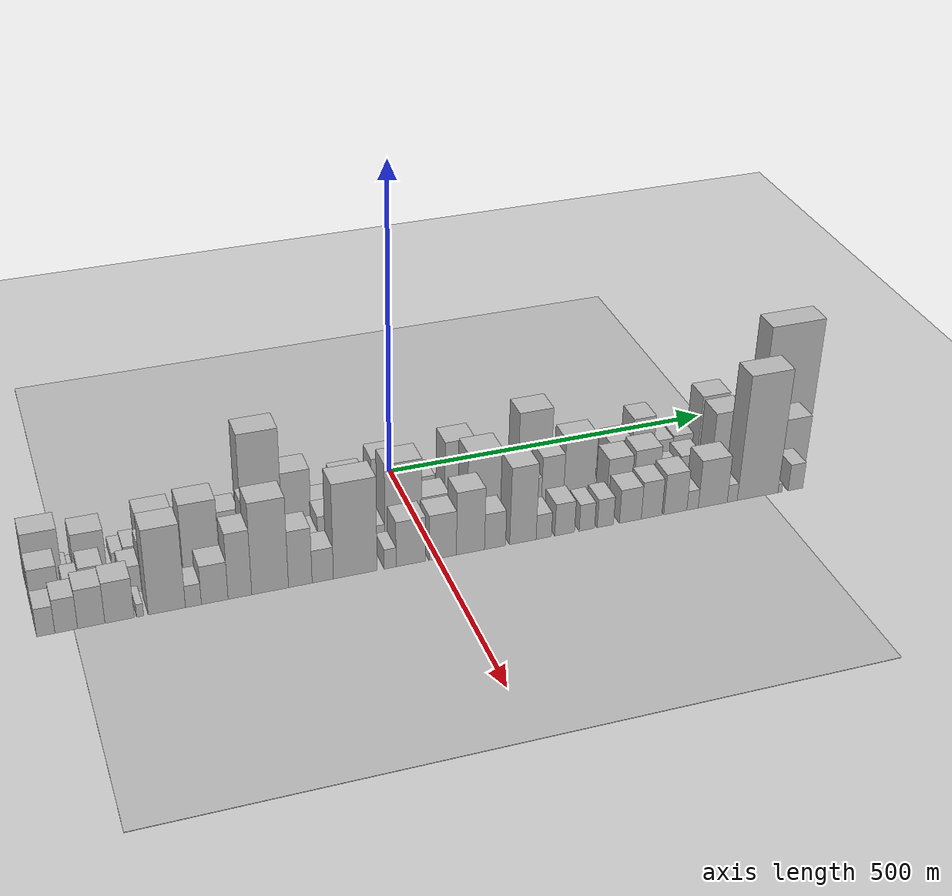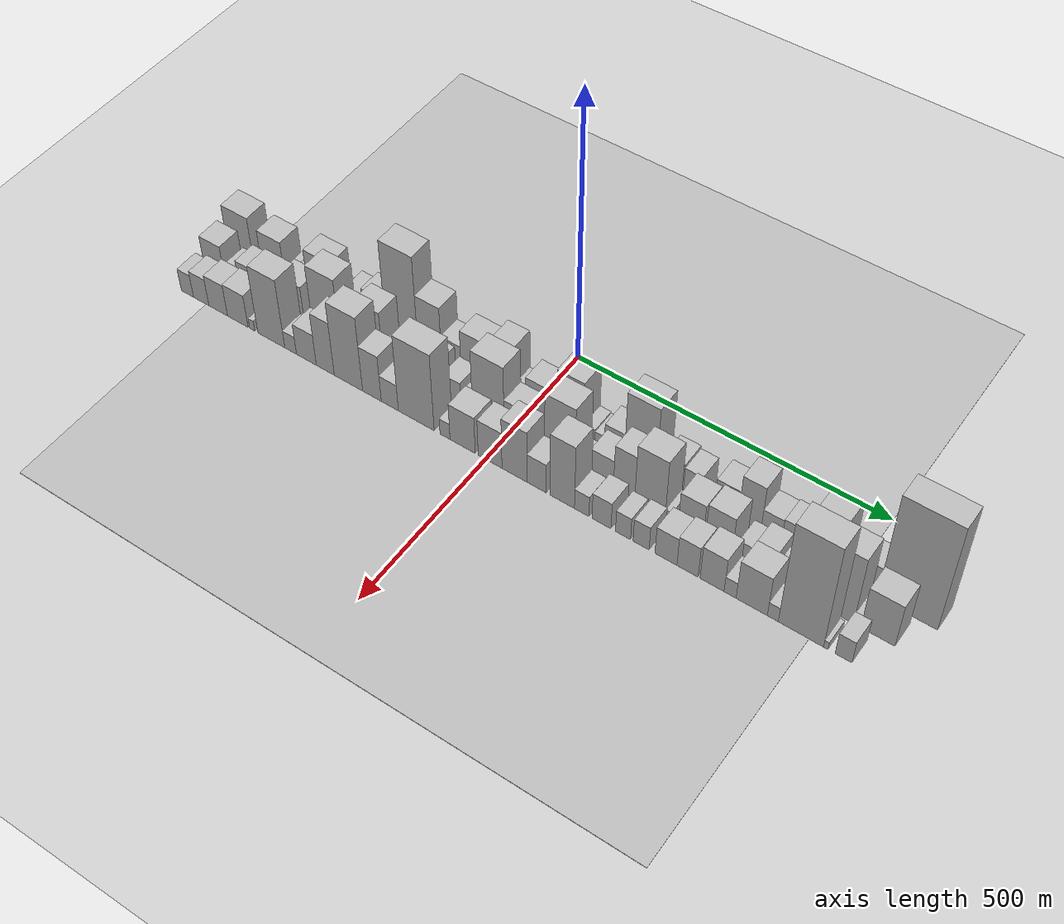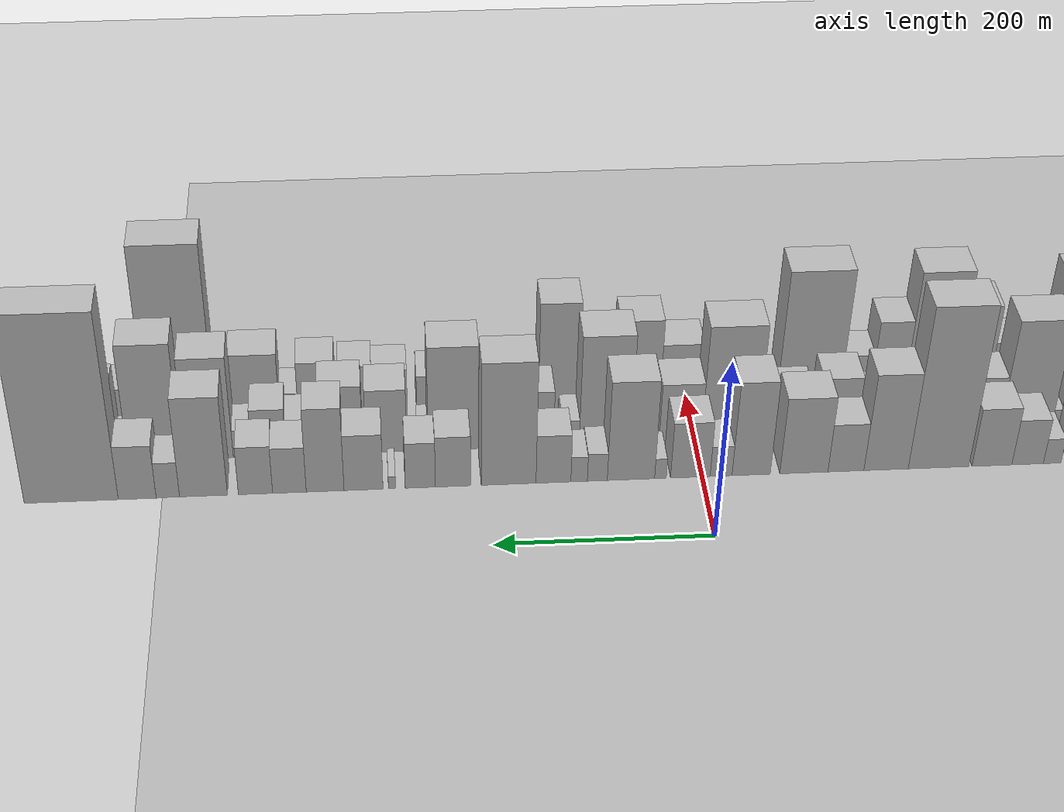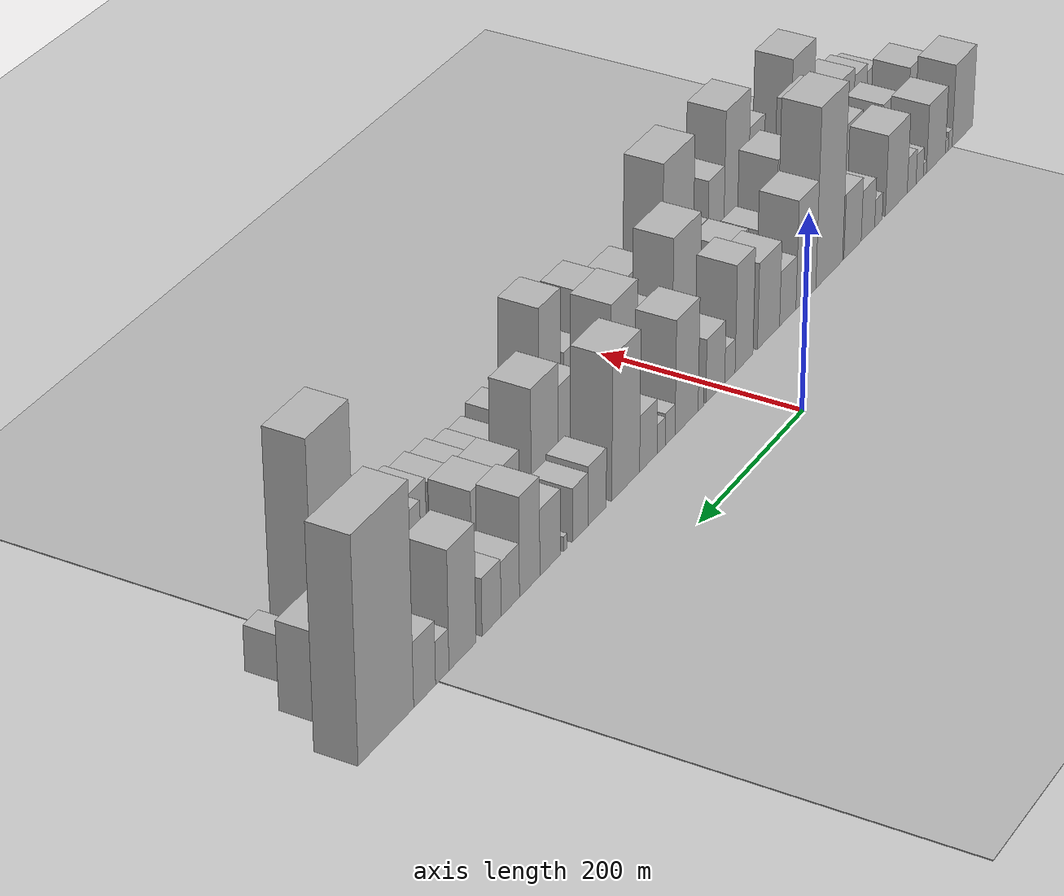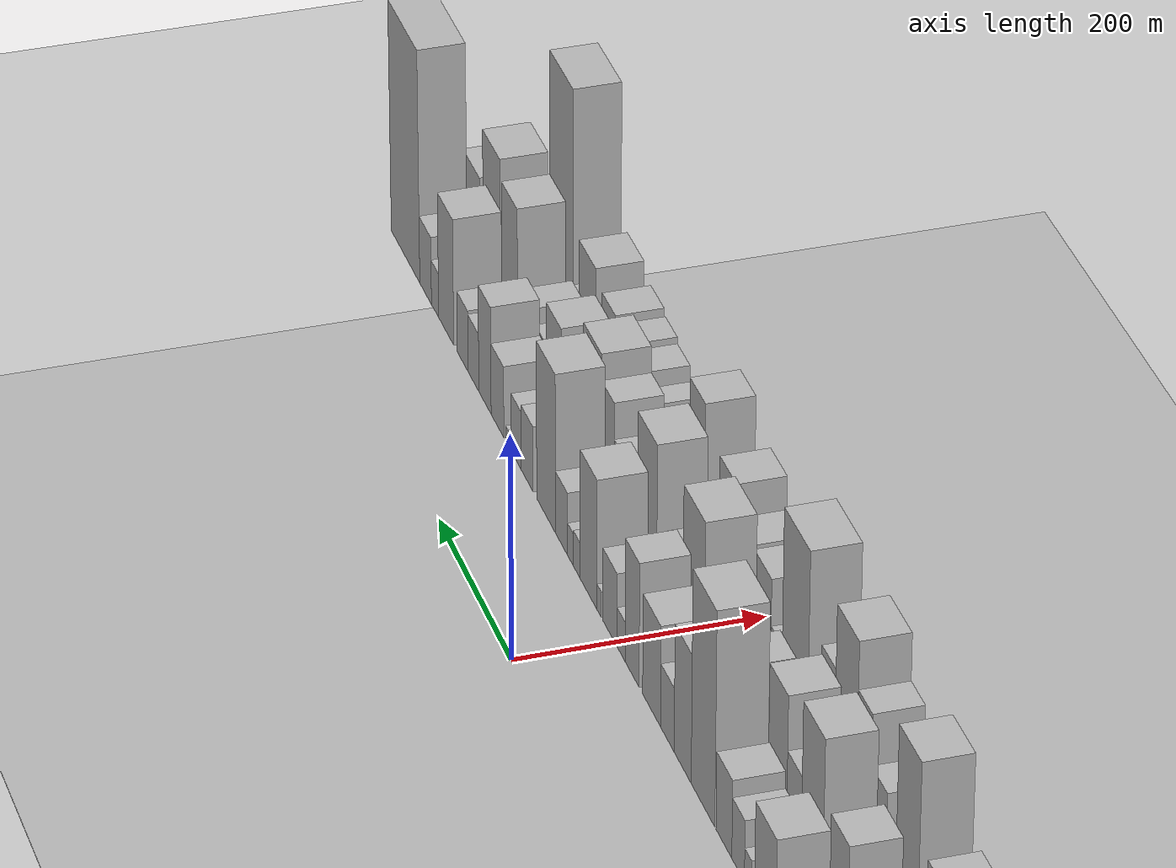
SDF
<?xml version="1.0" encoding="utf-8"?>

<sdf version="1.6">

   <world name="default">

      <gui fullscreen="0">

         <camera name="user_camera">

            <pose>-15 0 4.57585 0 0 0</pose>

            <view_controller>orbit</view_controller>

         </camera>

      </gui>

      <scene>

         <sky>

           <clouds>

             <speed>12</speed>

           </clouds>

         </sky>

         <ambient>0.4 0.4 0.4 1</ambient>

         <background>0.7 0.7 0.7 1</background>

         <shadows>1</shadows>

      </scene>

      <gravity>0 0 -9.8066</gravity>

      <magnetic_field>6e-06 2.3e-05 -4.2e-05</magnetic_field>

      <physics default="0" name="default_physics" type="ode">

         <ode>

            <solver>

               <type>quick</type>

               <iters>10</iters>

               <sor>1.0</sor>

               <use_dynamic_moi_rescaling>0</use_dynamic_moi_rescaling>

            </solver>

            <constraints>

               <cfm>0</cfm>

               <erp>0.2</erp>

               <contact_max_correcting_vel>100</contact_max_correcting_vel>

               <contact_surface_layer>0.001</contact_surface_layer>

            </constraints>

         </ode>

         <max_step_size>0.004</max_step_size>

         <real_time_factor>1</real_time_factor>

         <real_time_update_rate>250</real_time_update_rate>

      </physics>

      <light name="sun" type="directional">

         <cast_shadows>1</cast_shadows>

         <pose>0 0 10 0 0 0</pose>

         <diffuse>0.8 0.8 0.8 1</diffuse>

         <specular>0.2 0.2 0.2 1</specular>

         <attenuation>

            <range>1000</range>

            <constant>0.9</constant>

            <linear>0.01</linear>

            <quadratic>0.001</quadratic>

         </attenuation>

         <direction>-0.5 0.1 -0.9</direction>

      </light>

      <include>

         <name>ground_plane_1</name>

         <uri>model://HANNAS_ground_plane</uri>

         <pose>0 0 0  0 0 0</pose>

      </include>

      <include>

         <name>ground_plane_2</name>

         <uri>model://HANNAS_ground_plane</uri>

         <pose>100 0 0  0 0 0</pose>

      </include>

      <model name="building_1">

         <static>1</static>

         <pose frame="">100.0000 -523.3896 0 0.000000 0.000000 0.000000</pose>

         <link name="link">

            <pose frame="">0 0 45.00 0 0 0</pose>

            <collision name="collision">

               <geometry>

                  <box>

                     <size>40.0000 49.2209 90.0000</size>

                  </box>

               </geometry>

               <max_contacts>10</max_contacts>

               <surface>

                  <contact>

                     <ode/>

                  </contact>

                  <bounce/>

                  <friction>

                     <torsional>

                        <ode/>

                     </torsional>

                     <ode/>

                  </friction>

               </surface>

            </collision>

            <visual name="visual">

               <cast_shadows>0</cast_shadows>

               <geometry>

                  <box>

                     <size>40.0000 49.2209 90.0000</size>

                  </box>

               </geometry>

               <material>

                  <script>

                     <uri>model://HANNAS_wall/materials/scripts</uri>

                     <uri>model://HANNAS_wall/materials/textures</uri>

                     <name>vrc/HANNAS_wall</name>

                  </script>

               </material>

            </visual>

            <self_collide>0</self_collide>

            <enable_wind>0</enable_wind>

            <kinematic>0</kinematic>

         </link>

      </model>

      <model name="building_2">

         <static>1</static>

         <pose frame="">100.0000 -494.3995 0 0.000000 0.000000 0.000000</pose>

         <link name="link">

            <pose frame="">0 0 10.50 0 0 0</pose>

            <collision name="collision">

               <geometry>

                  <box>

                     <size>40.0000 8.7592 21.0000</size>

                  </box>

               </geometry>

               <max_contacts>10</max_contacts>

               <surface>

                  <contact>

                     <ode/>

                  </contact>

                  <bounce/>

                  <friction>

                     <torsional>

                        <ode/>

                     </torsional>

                     <ode/>

                  </friction>

               </surface>

            </collision>

            <visual name="visual">

               <cast_shadows>0</cast_shadows>

               <geometry>

                  <box>

                     <size>40.0000 8.7592 21.0000</size>

                  </box>

               </geometry>

               <material>

                  <script>

                     <uri>model://HANNAS_wall/materials/scripts</uri>

                     <uri>model://HANNAS_wall/materials/textures</uri>

                     <name>vrc/HANNAS_wall</name>

                  </script>

               </material>

            </visual>

            <self_collide>0</self_collide>

            <enable_wind>0</enable_wind>

            <kinematic>0</kinematic>

         </link>

      </model>

      <model name="building_3">

         <static>1</static>

         <pose frame="">100.0000 -486.4066 0 0.000000 0.000000 0.000000</pose>

         <link name="link">

            <pose frame="">0 0 7.50 0 0 0</pose>

            <collision name="collision">

               <geometry>

                  <box>

                     <size>40.0000 7.2267 15.0000</size>

                  </box>

               </geometry>

               <max_contacts>10</max_contacts>

               <surface>

                  <contact>

                     <ode/>

                  </contact>

                  <bounce/>

                  <friction>

                     <torsional>

                        <ode/>

                     </torsional>

                     <ode/>

                  </friction>

               </surface>

            </collision>

            <visual name="visual">

               <cast_shadows>0</cast_shadows>

               <geometry>

                  <box>

                     <size>40.0000 7.2267 15.0000</size>

                  </box>

               </geometry>

               <material>

                  <script>

                     <uri>model://HANNAS_wall/materials/scripts</uri>

                     <uri>model://HANNAS_wall/materials/textures</uri>

                     <name>vrc/HANNAS_wall</name>

                  </script>

               </material>

            </visual>

            <self_collide>0</self_collide>

            <enable_wind>0</enable_wind>

            <kinematic>0</kinematic>

         </link>

      </model>

      <model name="building_4">

         <static>1</static>

         <pose frame="">100.0000 -460.7162 0 0.000000 0.000000 0.000000</pose>

         <link name="link">

            <pose frame="">0 0 37.50 0 0 0</pose>

            <collision name="collision">

               <geometry>

                  <box>

                     <size>40.0000 44.1541 75.0000</size>

                  </box>

               </geometry>

               <max_contacts>10</max_contacts>

               <surface>

                  <contact>

                     <ode/>

                  </contact>

                  <bounce/>

                  <friction>

                     <torsional>

                        <ode/>

                     </torsional>

                     <ode/>

                  </friction>

               </surface>

            </collision>

            <visual name="visual">

               <cast_shadows>0</cast_shadows>

               <geometry>

                  <box>

                     <size>40.0000 44.1541 75.0000</size>

                  </box>

               </geometry>

               <material>

                  <script>

                     <uri>model://HANNAS_wall/materials/scripts</uri>

                     <uri>model://HANNAS_wall/materials/textures</uri>

                     <name>vrc/HANNAS_wall</name>

                  </script>

               </material>

            </visual>

            <self_collide>0</self_collide>

            <enable_wind>0</enable_wind>

            <kinematic>0</kinematic>

         </link>

      </model>

      <model name="building_5">

         <static>1</static>

         <pose frame="">100.0000 -434.9563 0 0.000000 0.000000 0.000000</pose>

         <link name="link">

            <pose frame="">0 0 7.50 0 0 0</pose>

            <collision name="collision">

               <geometry>

                  <box>

                     <size>40.0000 7.3657 15.0000</size>

                  </box>

               </geometry>

               <max_contacts>10</max_contacts>

               <surface>

                  <contact>

                     <ode/>

                  </contact>

                  <bounce/>

                  <friction>

                     <torsional>

                        <ode/>

                     </torsional>

                     <ode/>

                  </friction>

               </surface>

            </collision>

            <visual name="visual">

               <cast_shadows>0</cast_shadows>

               <geometry>

                  <box>

                     <size>40.0000 7.3657 15.0000</size>

                  </box>

               </geometry>

               <material>

                  <script>

                     <uri>model://HANNAS_wall/materials/scripts</uri>

                     <uri>model://HANNAS_wall/materials/textures</uri>

                     <name>vrc/HANNAS_wall</name>

                  </script>

               </material>

            </visual>

            <self_collide>0</self_collide>

            <enable_wind>0</enable_wind>

            <kinematic>0</kinematic>

         </link>

      </model>

      <model name="building_6">

         <static>1</static>

         <pose frame="">100.0000 -422.9179 0 0.000000 0.000000 0.000000</pose>

         <link name="link">

            <pose frame="">0 0 16.50 0 0 0</pose>

            <collision name="collision">

               <geometry>

                  <box>

                     <size>40.0000 16.7111 33.0000</size>

                  </box>

               </geometry>

               <max_contacts>10</max_contacts>

               <surface>

                  <contact>

                     <ode/>

                  </contact>

                  <bounce/>

                  <friction>

                     <torsional>

                        <ode/>

                     </torsional>

                     <ode/>

                  </friction>

               </surface>

            </collision>

            <visual name="visual">

               <cast_shadows>0</cast_shadows>

               <geometry>

                  <box>

                     <size>40.0000 16.7111 33.0000</size>

                  </box>

               </geometry>

               <material>

                  <script>

                     <uri>model://HANNAS_wall/materials/scripts</uri>

                     <uri>model://HANNAS_wall/materials/textures</uri>

                     <name>vrc/HANNAS_wall</name>

                  </script>

               </material>

            </visual>

            <self_collide>0</self_collide>

            <enable_wind>0</enable_wind>

            <kinematic>0</kinematic>

         </link>

      </model>

      <model name="building_7">

         <static>1</static>

         <pose frame="">100.0000 -404.4449 0 0.000000 0.000000 0.000000</pose>

         <link name="link">

            <pose frame="">0 0 19.50 0 0 0</pose>

            <collision name="collision">

               <geometry>

                  <box>

                     <size>40.0000 20.2349 39.0000</size>

                  </box>

               </geometry>

               <max_contacts>10</max_contacts>

               <surface>

                  <contact>

                     <ode/>

                  </contact>

                  <bounce/>

                  <friction>

                     <torsional>

                        <ode/>

                     </torsional>

                     <ode/>

                  </friction>

               </surface>

            </collision>

            <visual name="visual">

               <cast_shadows>0</cast_shadows>

               <geometry>

                  <box>

                     <size>40.0000 20.2349 39.0000</size>

                  </box>

               </geometry>

               <material>

                  <script>

                     <uri>model://HANNAS_wall/materials/scripts</uri>

                     <uri>model://HANNAS_wall/materials/textures</uri>

                     <name>vrc/HANNAS_wall</name>

                  </script>

               </material>

            </visual>

            <self_collide>0</self_collide>

            <enable_wind>0</enable_wind>

            <kinematic>0</kinematic>

         </link>

      </model>

      <model name="building_8">

         <static>1</static>

         <pose frame="">100.0000 -369.5859 0 0.000000 0.000000 0.000000</pose>

         <link name="link">

            <pose frame="">0 0 43.50 0 0 0</pose>

            <collision name="collision">

               <geometry>

                  <box>

                     <size>40.0000 49.4830 87.0000</size>

                  </box>

               </geometry>

               <max_contacts>10</max_contacts>

               <surface>

                  <contact>

                     <ode/>

                  </contact>

                  <bounce/>

                  <friction>

                     <torsional>

                        <ode/>

                     </torsional>

                     <ode/>

                  </friction>

               </surface>

            </collision>

            <visual name="visual">

               <cast_shadows>0</cast_shadows>

               <geometry>

                  <box>

                     <size>40.0000 49.4830 87.0000</size>

                  </box>

               </geometry>

               <material>

                  <script>

                     <uri>model://HANNAS_wall/materials/scripts</uri>

                     <uri>model://HANNAS_wall/materials/textures</uri>

                     <name>vrc/HANNAS_wall</name>

                  </script>

               </material>

            </visual>

            <self_collide>0</self_collide>

            <enable_wind>0</enable_wind>

            <kinematic>0</kinematic>

         </link>

      </model>

      <model name="building_9">

         <static>1</static>

         <pose frame="">100.0000 -329.4801 0 0.000000 0.000000 0.000000</pose>

         <link name="link">

            <pose frame="">0 0 15.00 0 0 0</pose>

            <collision name="collision">

               <geometry>

                  <box>

                     <size>40.0000 16.7286 30.0000</size>

                  </box>

               </geometry>

               <max_contacts>10</max_contacts>

               <surface>

                  <contact>

                     <ode/>

                  </contact>

                  <bounce/>

                  <friction>

                     <torsional>

                        <ode/>

                     </torsional>

                     <ode/>

                  </friction>

               </surface>

            </collision>

            <visual name="visual">

               <cast_shadows>0</cast_shadows>

               <geometry>

                  <box>

                     <size>40.0000 16.7286 30.0000</size>

                  </box>

               </geometry>

               <material>

                  <script>

                     <uri>model://HANNAS_wall/materials/scripts</uri>

                     <uri>model://HANNAS_wall/materials/textures</uri>

                     <name>vrc/HANNAS_wall</name>

                  </script>

               </material>

            </visual>

            <self_collide>0</self_collide>

            <enable_wind>0</enable_wind>

            <kinematic>0</kinematic>

         </link>

      </model>

      <model name="building_10">

         <static>1</static>

         <pose frame="">100.0000 -306.1747 0 0.000000 0.000000 0.000000</pose>

         <link name="link">

            <pose frame="">0 0 27.00 0 0 0</pose>

            <collision name="collision">

               <geometry>

                  <box>

                     <size>40.0000 29.8823 54.0000</size>

                  </box>

               </geometry>

               <max_contacts>10</max_contacts>

               <surface>

                  <contact>

                     <ode/>

                  </contact>

                  <bounce/>

                  <friction>

                     <torsional>

                        <ode/>

                     </torsional>

                     <ode/>

                  </friction>

               </surface>

            </collision>

            <visual name="visual">

               <cast_shadows>0</cast_shadows>

               <geometry>

                  <box>

                     <size>40.0000 29.8823 54.0000</size>

                  </box>

               </geometry>

               <material>

                  <script>

                     <uri>model://HANNAS_wall/materials/scripts</uri>

                     <uri>model://HANNAS_wall/materials/textures</uri>

                     <name>vrc/HANNAS_wall</name>

                  </script>

               </material>

            </visual>

            <self_collide>0</self_collide>

            <enable_wind>0</enable_wind>

            <kinematic>0</kinematic>

         </link>

      </model>

      <model name="building_11">

         <static>1</static>

         <pose frame="">100.0000 -272.3612 0 0.000000 0.000000 0.000000</pose>

         <link name="link">

            <pose frame="">0 0 34.50 0 0 0</pose>

            <collision name="collision">

               <geometry>

                  <box>

                     <size>40.0000 37.7446 69.0000</size>

                  </box>

               </geometry>

               <max_contacts>10</max_contacts>

               <surface>

                  <contact>

                     <ode/>

                  </contact>

                  <bounce/>

                  <friction>

                     <torsional>

                        <ode/>

                     </torsional>

                     <ode/>

                  </friction>

               </surface>

            </collision>

            <visual name="visual">

               <cast_shadows>0</cast_shadows>

               <geometry>

                  <box>

                     <size>40.0000 37.7446 69.0000</size>

                  </box>

               </geometry>

               <material>

                  <script>

                     <uri>model://HANNAS_wall/materials/scripts</uri>

                     <uri>model://HANNAS_wall/materials/textures</uri>

                     <name>vrc/HANNAS_wall</name>

                  </script>

               </material>

            </visual>

            <self_collide>0</self_collide>

            <enable_wind>0</enable_wind>

            <kinematic>0</kinematic>

         </link>

      </model>

      <model name="building_12">

         <static>1</static>

         <pose frame="">100.0000 -221.8321 0 0.000000 0.000000 0.000000</pose>

         <link name="link">

            <pose frame="">0 0 94.50 0 0 0</pose>

            <collision name="collision">

               <geometry>

                  <box>

                     <size>40.0000 57.3137 189.0000</size>

                  </box>

               </geometry>

               <max_contacts>10</max_contacts>

               <surface>

                  <contact>

                     <ode/>

                  </contact>

                  <bounce/>

                  <friction>

                     <torsional>

                        <ode/>

                     </torsional>

                     <ode/>

                  </friction>

               </surface>

            </collision>

            <visual name="visual">

               <cast_shadows>0</cast_shadows>

               <geometry>

                  <box>

                     <size>40.0000 57.3137 189.0000</size>

                  </box>

               </geometry>

               <material>

                  <script>

                     <uri>model://HANNAS_wall/materials/scripts</uri>

                     <uri>model://HANNAS_wall/materials/textures</uri>

                     <name>vrc/HANNAS_wall</name>

                  </script>

               </material>

            </visual>

            <self_collide>0</self_collide>

            <enable_wind>0</enable_wind>

            <kinematic>0</kinematic>

         </link>

      </model>

      <model name="building_13">

         <static>1</static>

         <pose frame="">100.0000 -172.2524 0 0.000000 0.000000 0.000000</pose>

         <link name="link">

            <pose frame="">0 0 57.00 0 0 0</pose>

            <collision name="collision">

               <geometry>

                  <box>

                     <size>40.0000 41.8458 114.0000</size>

                  </box>

               </geometry>

               <max_contacts>10</max_contacts>

               <surface>

                  <contact>

                     <ode/>

                  </contact>

                  <bounce/>

                  <friction>

                     <torsional>

                        <ode/>

                     </torsional>

                     <ode/>

                  </friction>

               </surface>

            </collision>

            <visual name="visual">

               <cast_shadows>0</cast_shadows>

               <geometry>

                  <box>

                     <size>40.0000 41.8458 114.0000</size>

                  </box>

               </geometry>

               <material>

                  <script>

                     <uri>model://HANNAS_wall/materials/scripts</uri>

                     <uri>model://HANNAS_wall/materials/textures</uri>

                     <name>vrc/HANNAS_wall</name>

                  </script>

               </material>

            </visual>

            <self_collide>0</self_collide>

            <enable_wind>0</enable_wind>

            <kinematic>0</kinematic>

         </link>

      </model>

      <model name="building_14">

         <static>1</static>

         <pose frame="">100.0000 -134.3879 0 0.000000 0.000000 0.000000</pose>

         <link name="link">

            <pose frame="">0 0 28.50 0 0 0</pose>

            <collision name="collision">

               <geometry>

                  <box>

                     <size>40.0000 33.8833 57.0000</size>

                  </box>

               </geometry>

               <max_contacts>10</max_contacts>

               <surface>

                  <contact>

                     <ode/>

                  </contact>

                  <bounce/>

                  <friction>

                     <torsional>

                        <ode/>

                     </torsional>

                     <ode/>

                  </friction>

               </surface>

            </collision>

            <visual name="visual">

               <cast_shadows>0</cast_shadows>

               <geometry>

                  <box>

                     <size>40.0000 33.8833 57.0000</size>

                  </box>

               </geometry>

               <material>

                  <script>

                     <uri>model://HANNAS_wall/materials/scripts</uri>

                     <uri>model://HANNAS_wall/materials/textures</uri>

                     <name>vrc/HANNAS_wall</name>

                  </script>

               </material>

            </visual>

            <self_collide>0</self_collide>

            <enable_wind>0</enable_wind>

            <kinematic>0</kinematic>

         </link>

      </model>

      <model name="building_15">

         <static>1</static>

         <pose frame="">100.0000 -94.8387 0 0.000000 0.000000 0.000000</pose>

         <link name="link">

            <pose frame="">0 0 45.00 0 0 0</pose>

            <collision name="collision">

               <geometry>

                  <box>

                     <size>40.0000 45.2150 90.0000</size>

                  </box>

               </geometry>

               <max_contacts>10</max_contacts>

               <surface>

                  <contact>

                     <ode/>

                  </contact>

                  <bounce/>

                  <friction>

                     <torsional>

                        <ode/>

                     </torsional>

                     <ode/>

                  </friction>

               </surface>

            </collision>

            <visual name="visual">

               <cast_shadows>0</cast_shadows>

               <geometry>

                  <box>

                     <size>40.0000 45.2150 90.0000</size>

                  </box>

               </geometry>

               <material>

                  <script>

                     <uri>model://HANNAS_wall/materials/scripts</uri>

                     <uri>model://HANNAS_wall/materials/textures</uri>

                     <name>vrc/HANNAS_wall</name>

                  </script>

               </material>

            </visual>

            <self_collide>0</self_collide>

            <enable_wind>0</enable_wind>

            <kinematic>0</kinematic>

         </link>

      </model>

      <model name="building_16">

         <static>1</static>

         <pose frame="">100.0000 -45.3089 0 0.000000 0.000000 0.000000</pose>

         <link name="link">

            <pose frame="">0 0 55.50 0 0 0</pose>

            <collision name="collision">

               <geometry>

                  <box>

                     <size>40.0000 35.8447 111.0000</size>

                  </box>

               </geometry>

               <max_contacts>10</max_contacts>

               <surface>

                  <contact>

                     <ode/>

                  </contact>

                  <bounce/>

                  <friction>

                     <torsional>

                        <ode/>

                     </torsional>

                     <ode/>

                  </friction>

               </surface>

            </collision>

            <visual name="visual">

               <cast_shadows>0</cast_shadows>

               <geometry>

                  <box>

                     <size>40.0000 35.8447 111.0000</size>

                  </box>

               </geometry>

               <material>

                  <script>

                     <uri>model://HANNAS_wall/materials/scripts</uri>

                     <uri>model://HANNAS_wall/materials/textures</uri>

                     <name>vrc/HANNAS_wall</name>

                  </script>

               </material>

            </visual>

            <self_collide>0</self_collide>

            <enable_wind>0</enable_wind>

            <kinematic>0</kinematic>

         </link>

      </model>

      <model name="building_17">

         <static>1</static>

         <pose frame="">100.0000 -17.1245 0 0.000000 0.000000 0.000000</pose>

         <link name="link">

            <pose frame="">0 0 18.00 0 0 0</pose>

            <collision name="collision">

               <geometry>

                  <box>

                     <size>40.0000 20.5241 36.0000</size>

                  </box>

               </geometry>

               <max_contacts>10</max_contacts>

               <surface>

                  <contact>

                     <ode/>

                  </contact>

                  <bounce/>

                  <friction>

                     <torsional>

                        <ode/>

                     </torsional>

                     <ode/>

                  </friction>

               </surface>

            </collision>

            <visual name="visual">

               <cast_shadows>0</cast_shadows>

               <geometry>

                  <box>

                     <size>40.0000 20.5241 36.0000</size>

                  </box>

               </geometry>

               <material>

                  <script>

                     <uri>model://HANNAS_wall/materials/scripts</uri>

                     <uri>model://HANNAS_wall/materials/textures</uri>

                     <name>vrc/HANNAS_wall</name>

                  </script>

               </material>

            </visual>

            <self_collide>0</self_collide>

            <enable_wind>0</enable_wind>

            <kinematic>0</kinematic>

         </link>

      </model>

      <model name="building_18">

         <static>1</static>

         <pose frame="">100.0000 11.6222 0 0.000000 0.000000 0.000000</pose>

         <link name="link">

            <pose frame="">0 0 33.00 0 0 0</pose>

            <collision name="collision">

               <geometry>

                  <box>

                     <size>40.0000 36.9693 66.0000</size>

                  </box>

               </geometry>

               <max_contacts>10</max_contacts>

               <surface>

                  <contact>

                     <ode/>

                  </contact>

                  <bounce/>

                  <friction>

                     <torsional>

                        <ode/>

                     </torsional>

                     <ode/>

                  </friction>

               </surface>

            </collision>

            <visual name="visual">

               <cast_shadows>0</cast_shadows>

               <geometry>

                  <box>

                     <size>40.0000 36.9693 66.0000</size>

                  </box>

               </geometry>

               <material>

                  <script>

                     <uri>model://HANNAS_wall/materials/scripts</uri>

                     <uri>model://HANNAS_wall/materials/textures</uri>

                     <name>vrc/HANNAS_wall</name>

                  </script>

               </material>

            </visual>

            <self_collide>0</self_collide>

            <enable_wind>0</enable_wind>

            <kinematic>0</kinematic>

         </link>

      </model>

      <model name="building_19">

         <static>1</static>

         <pose frame="">100.0000 39.5540 0 0.000000 0.000000 0.000000</pose>

         <link name="link">

            <pose frame="">0 0 12.00 0 0 0</pose>

            <collision name="collision">

               <geometry>

                  <box>

                     <size>40.0000 10.8943 24.0000</size>

                  </box>

               </geometry>

               <max_contacts>10</max_contacts>

               <surface>

                  <contact>

                     <ode/>

                  </contact>

                  <bounce/>

                  <friction>

                     <torsional>

                        <ode/>

                     </torsional>

                     <ode/>

                  </friction>

               </surface>

            </collision>

            <visual name="visual">

               <cast_shadows>0</cast_shadows>

               <geometry>

                  <box>

                     <size>40.0000 10.8943 24.0000</size>

                  </box>

               </geometry>

               <material>

                  <script>

                     <uri>model://HANNAS_wall/materials/scripts</uri>

                     <uri>model://HANNAS_wall/materials/textures</uri>

                     <name>vrc/HANNAS_wall</name>

                  </script>

               </material>

            </visual>

            <self_collide>0</self_collide>

            <enable_wind>0</enable_wind>

            <kinematic>0</kinematic>

         </link>

      </model>

      <model name="building_20">

         <static>1</static>

         <pose frame="">100.0000 67.0871 0 0.000000 0.000000 0.000000</pose>

         <link name="link">

            <pose frame="">0 0 58.50 0 0 0</pose>

            <collision name="collision">

               <geometry>

                  <box>

                     <size>40.0000 44.1720 117.0000</size>

                  </box>

               </geometry>

               <max_contacts>10</max_contacts>

               <surface>

                  <contact>

                     <ode/>

                  </contact>

                  <bounce/>

                  <friction>

                     <torsional>

                        <ode/>

                     </torsional>

                     <ode/>

                  </friction>

               </surface>

            </collision>

            <visual name="visual">

               <cast_shadows>0</cast_shadows>

               <geometry>

                  <box>

                     <size>40.0000 44.1720 117.0000</size>

                  </box>

               </geometry>

               <material>

                  <script>

                     <uri>model://HANNAS_wall/materials/scripts</uri>

                     <uri>model://HANNAS_wall/materials/textures</uri>

                     <name>vrc/HANNAS_wall</name>

                  </script>

               </material>

            </visual>

            <self_collide>0</self_collide>

            <enable_wind>0</enable_wind>

            <kinematic>0</kinematic>

         </link>

      </model>

      <model name="building_21">

         <static>1</static>

         <pose frame="">100.0000 98.4633 0 0.000000 0.000000 0.000000</pose>

         <link name="link">

            <pose frame="">0 0 16.50 0 0 0</pose>

            <collision name="collision">

               <geometry>

                  <box>

                     <size>40.0000 18.5803 33.0000</size>

                  </box>

               </geometry>

               <max_contacts>10</max_contacts>

               <surface>

                  <contact>

                     <ode/>

                  </contact>

                  <bounce/>

                  <friction>

                     <torsional>

                        <ode/>

                     </torsional>

                     <ode/>

                  </friction>

               </surface>

            </collision>

            <visual name="visual">

               <cast_shadows>0</cast_shadows>

               <geometry>

                  <box>

                     <size>40.0000 18.5803 33.0000</size>

                  </box>

               </geometry>

               <material>

                  <script>

                     <uri>model://HANNAS_wall/materials/scripts</uri>

                     <uri>model://HANNAS_wall/materials/textures</uri>

                     <name>vrc/HANNAS_wall</name>

                  </script>

               </material>

            </visual>

            <self_collide>0</self_collide>

            <enable_wind>0</enable_wind>

            <kinematic>0</kinematic>

         </link>

      </model>

      <model name="building_22">

         <static>1</static>

         <pose frame="">100.0000 115.4284 0 0.000000 0.000000 0.000000</pose>

         <link name="link">

            <pose frame="">0 0 15.00 0 0 0</pose>

            <collision name="collision">

               <geometry>

                  <box>

                     <size>40.0000 15.3501 30.0000</size>

                  </box>

               </geometry>

               <max_contacts>10</max_contacts>

               <surface>

                  <contact>

                     <ode/>

                  </contact>

                  <bounce/>

                  <friction>

                     <torsional>

                        <ode/>

                     </torsional>

                     <ode/>

                  </friction>

               </surface>

            </collision>

            <visual name="visual">

               <cast_shadows>0</cast_shadows>

               <geometry>

                  <box>

                     <size>40.0000 15.3501 30.0000</size>

                  </box>

               </geometry>

               <material>

                  <script>

                     <uri>model://HANNAS_wall/materials/scripts</uri>

                     <uri>model://HANNAS_wall/materials/textures</uri>

                     <name>vrc/HANNAS_wall</name>

                  </script>

               </material>

            </visual>

            <self_collide>0</self_collide>

            <enable_wind>0</enable_wind>

            <kinematic>0</kinematic>

         </link>

      </model>

      <model name="building_23">

         <static>1</static>

         <pose frame="">100.0000 139.3123 0 0.000000 0.000000 0.000000</pose>

         <link name="link">

            <pose frame="">0 0 28.50 0 0 0</pose>

            <collision name="collision">

               <geometry>

                  <box>

                     <size>40.0000 32.4177 57.0000</size>

                  </box>

               </geometry>

               <max_contacts>10</max_contacts>

               <surface>

                  <contact>

                     <ode/>

                  </contact>

                  <bounce/>

                  <friction>

                     <torsional>

                        <ode/>

                     </torsional>

                     <ode/>

                  </friction>

               </surface>

            </collision>

            <visual name="visual">

               <cast_shadows>0</cast_shadows>

               <geometry>

                  <box>

                     <size>40.0000 32.4177 57.0000</size>

                  </box>

               </geometry>

               <material>

                  <script>

                     <uri>model://HANNAS_wall/materials/scripts</uri>

                     <uri>model://HANNAS_wall/materials/textures</uri>

                     <name>vrc/HANNAS_wall</name>

                  </script>

               </material>

            </visual>

            <self_collide>0</self_collide>

            <enable_wind>0</enable_wind>

            <kinematic>0</kinematic>

         </link>

      </model>

      <model name="building_24">

         <static>1</static>

         <pose frame="">100.0000 180.9041 0 0.000000 0.000000 0.000000</pose>

         <link name="link">

            <pose frame="">0 0 72.00 0 0 0</pose>

            <collision name="collision">

               <geometry>

                  <box>

                     <size>40.0000 50.7659 144.0000</size>

                  </box>

               </geometry>

               <max_contacts>10</max_contacts>

               <surface>

                  <contact>

                     <ode/>

                  </contact>

                  <bounce/>

                  <friction>

                     <torsional>

                        <ode/>

                     </torsional>

                     <ode/>

                  </friction>

               </surface>

            </collision>

            <visual name="visual">

               <cast_shadows>0</cast_shadows>

               <geometry>

                  <box>

                     <size>40.0000 50.7659 144.0000</size>

                  </box>

               </geometry>

               <material>

                  <script>

                     <uri>model://HANNAS_wall/materials/scripts</uri>

                     <uri>model://HANNAS_wall/materials/textures</uri>

                     <name>vrc/HANNAS_wall</name>

                  </script>

               </material>

            </visual>

            <self_collide>0</self_collide>

            <enable_wind>0</enable_wind>

            <kinematic>0</kinematic>

         </link>

      </model>

      <model name="building_25">

         <static>1</static>

         <pose frame="">100.0000 232.5861 0 0.000000 0.000000 0.000000</pose>

         <link name="link">

            <pose frame="">0 0 30.00 0 0 0</pose>

            <collision name="collision">

               <geometry>

                  <box>

                     <size>40.0000 32.5981 60.0000</size>

                  </box>

               </geometry>

               <max_contacts>10</max_contacts>

               <surface>

                  <contact>

                     <ode/>

                  </contact>

                  <bounce/>

                  <friction>

                     <torsional>

                        <ode/>

                     </torsional>

                     <ode/>

                  </friction>

               </surface>

            </collision>

            <visual name="visual">

               <cast_shadows>0</cast_shadows>

               <geometry>

                  <box>

                     <size>40.0000 32.5981 60.0000</size>

                  </box>

               </geometry>

               <material>

                  <script>

                     <uri>model://HANNAS_wall/materials/scripts</uri>

                     <uri>model://HANNAS_wall/materials/textures</uri>

                     <name>vrc/HANNAS_wall</name>

                  </script>

               </material>

            </visual>

            <self_collide>0</self_collide>

            <enable_wind>0</enable_wind>

            <kinematic>0</kinematic>

         </link>

      </model>

      <model name="building_26">

         <static>1</static>

         <pose frame="">100.0000 262.7361 0 0.000000 0.000000 0.000000</pose>

         <link name="link">

            <pose frame="">0 0 27.00 0 0 0</pose>

            <collision name="collision">

               <geometry>

                  <box>

                     <size>40.0000 27.7021 54.0000</size>

                  </box>

               </geometry>

               <max_contacts>10</max_contacts>

               <surface>

                  <contact>

                     <ode/>

                  </contact>

                  <bounce/>

                  <friction>

                     <torsional>

                        <ode/>

                     </torsional>

                     <ode/>

                  </friction>

               </surface>

            </collision>

            <visual name="visual">

               <cast_shadows>0</cast_shadows>

               <geometry>

                  <box>

                     <size>40.0000 27.7021 54.0000</size>

                  </box>

               </geometry>

               <material>

                  <script>

                     <uri>model://HANNAS_wall/materials/scripts</uri>

                     <uri>model://HANNAS_wall/materials/textures</uri>

                     <name>vrc/HANNAS_wall</name>

                  </script>

               </material>

            </visual>

            <self_collide>0</self_collide>

            <enable_wind>0</enable_wind>

            <kinematic>0</kinematic>

         </link>

      </model>

      <model name="building_27">

         <static>1</static>

         <pose frame="">100.0000 288.8583 0 0.000000 0.000000 0.000000</pose>

         <link name="link">

            <pose frame="">0 0 7.50 0 0 0</pose>

            <collision name="collision">

               <geometry>

                  <box>

                     <size>40.0000 6.5422 15.0000</size>

                  </box>

               </geometry>

               <max_contacts>10</max_contacts>

               <surface>

                  <contact>

                     <ode/>

                  </contact>

                  <bounce/>

                  <friction>

                     <torsional>

                        <ode/>

                     </torsional>

                     <ode/>

                  </friction>

               </surface>

            </collision>

            <visual name="visual">

               <cast_shadows>0</cast_shadows>

               <geometry>

                  <box>

                     <size>40.0000 6.5422 15.0000</size>

                  </box>

               </geometry>

               <material>

                  <script>

                     <uri>model://HANNAS_wall/materials/scripts</uri>

                     <uri>model://HANNAS_wall/materials/textures</uri>

                     <name>vrc/HANNAS_wall</name>

                  </script>

               </material>

            </visual>

            <self_collide>0</self_collide>

            <enable_wind>0</enable_wind>

            <kinematic>0</kinematic>

         </link>

      </model>

      <model name="building_28">

         <static>1</static>

         <pose frame="">100.0000 315.1019 0 0.000000 0.000000 0.000000</pose>

         <link name="link">

            <pose frame="">0 0 33.00 0 0 0</pose>

            <collision name="collision">

               <geometry>

                  <box>

                     <size>40.0000 35.9450 66.0000</size>

                  </box>

               </geometry>

               <max_contacts>10</max_contacts>

               <surface>

                  <contact>

                     <ode/>

                  </contact>

                  <bounce/>

                  <friction>

                     <torsional>

                        <ode/>

                     </torsional>

                     <ode/>

                  </friction>

               </surface>

            </collision>

            <visual name="visual">

               <cast_shadows>0</cast_shadows>

               <geometry>

                  <box>

                     <size>40.0000 35.9450 66.0000</size>

                  </box>

               </geometry>

               <material>

                  <script>

                     <uri>model://HANNAS_wall/materials/scripts</uri>

                     <uri>model://HANNAS_wall/materials/textures</uri>

                     <name>vrc/HANNAS_wall</name>

                  </script>

               </material>

            </visual>

            <self_collide>0</self_collide>

            <enable_wind>0</enable_wind>

            <kinematic>0</kinematic>

         </link>

      </model>

      <model name="building_29">

         <static>1</static>

         <pose frame="">100.0000 350.4758 0 0.000000 0.000000 0.000000</pose>

         <link name="link">

            <pose frame="">0 0 49.50 0 0 0</pose>

            <collision name="collision">

               <geometry>

                  <box>

                     <size>40.0000 34.8028 99.0000</size>

                  </box>

               </geometry>

               <max_contacts>10</max_contacts>

               <surface>

                  <contact>

                     <ode/>

                  </contact>

                  <bounce/>

                  <friction>

                     <torsional>

                        <ode/>

                     </torsional>

                     <ode/>

                  </friction>

               </surface>

            </collision>

            <visual name="visual">

               <cast_shadows>0</cast_shadows>

               <geometry>

                  <box>

                     <size>40.0000 34.8028 99.0000</size>

                  </box>

               </geometry>

               <material>

                  <script>

                     <uri>model://HANNAS_wall/materials/scripts</uri>

                     <uri>model://HANNAS_wall/materials/textures</uri>

                     <name>vrc/HANNAS_wall</name>

                  </script>

               </material>

            </visual>

            <self_collide>0</self_collide>

            <enable_wind>0</enable_wind>

            <kinematic>0</kinematic>

         </link>

      </model>

      <model name="building_30">

         <static>1</static>

         <pose frame="">100.0000 383.3296 0 0.000000 0.000000 0.000000</pose>

         <link name="link">

            <pose frame="">0 0 27.00 0 0 0</pose>

            <collision name="collision">

               <geometry>

                  <box>

                     <size>40.0000 30.9048 54.0000</size>

                  </box>

               </geometry>

               <max_contacts>10</max_contacts>

               <surface>

                  <contact>

                     <ode/>

                  </contact>

                  <bounce/>

                  <friction>

                     <torsional>

                        <ode/>

                     </torsional>

                     <ode/>

                  </friction>

               </surface>

            </collision>

            <visual name="visual">

               <cast_shadows>0</cast_shadows>

               <geometry>

                  <box>

                     <size>40.0000 30.9048 54.0000</size>

                  </box>

               </geometry>

               <material>

                  <script>

                     <uri>model://HANNAS_wall/materials/scripts</uri>

                     <uri>model://HANNAS_wall/materials/textures</uri>

                     <name>vrc/HANNAS_wall</name>

                  </script>

               </material>

            </visual>

            <self_collide>0</self_collide>

            <enable_wind>0</enable_wind>

            <kinematic>0</kinematic>

         </link>

      </model>

      <model name="building_31">

         <static>1</static>

         <pose frame="">100.0000 414.5140 0 0.000000 0.000000 0.000000</pose>

         <link name="link">

            <pose frame="">0 0 28.50 0 0 0</pose>

            <collision name="collision">

               <geometry>

                  <box>

                     <size>40.0000 31.4638 57.0000</size>

                  </box>

               </geometry>

               <max_contacts>10</max_contacts>

               <surface>

                  <contact>

                     <ode/>

                  </contact>

                  <bounce/>

                  <friction>

                     <torsional>

                        <ode/>

                     </torsional>

                     <ode/>

                  </friction>

               </surface>

            </collision>

            <visual name="visual">

               <cast_shadows>0</cast_shadows>

               <geometry>

                  <box>

                     <size>40.0000 31.4638 57.0000</size>

                  </box>

               </geometry>

               <material>

                  <script>

                     <uri>model://HANNAS_wall/materials/scripts</uri>

                     <uri>model://HANNAS_wall/materials/textures</uri>

                     <name>vrc/HANNAS_wall</name>

                  </script>

               </material>

            </visual>

            <self_collide>0</self_collide>

            <enable_wind>0</enable_wind>

            <kinematic>0</kinematic>

         </link>

      </model>

      <model name="building_32">

         <static>1</static>

         <pose frame="">100.0000 462.1769 0 0.000000 0.000000 0.000000</pose>

         <link name="link">

            <pose frame="">0 0 58.50 0 0 0</pose>

            <collision name="collision">

               <geometry>

                  <box>

                     <size>40.0000 43.8621 117.0000</size>

                  </box>

               </geometry>

               <max_contacts>10</max_contacts>

               <surface>

                  <contact>

                     <ode/>

                  </contact>

                  <bounce/>

                  <friction>

                     <torsional>

                        <ode/>

                     </torsional>

                     <ode/>

                  </friction>

               </surface>

            </collision>

            <visual name="visual">

               <cast_shadows>0</cast_shadows>

               <geometry>

                  <box>

                     <size>40.0000 43.8621 117.0000</size>

                  </box>

               </geometry>

               <material>

                  <script>

                     <uri>model://HANNAS_wall/materials/scripts</uri>

                     <uri>model://HANNAS_wall/materials/textures</uri>

                     <name>vrc/HANNAS_wall</name>

                  </script>

               </material>

            </visual>

            <self_collide>0</self_collide>

            <enable_wind>0</enable_wind>

            <kinematic>0</kinematic>

         </link>

      </model>

      <model name="building_33">

         <static>1</static>

         <pose frame="">100.0000 494.8124 0 0.000000 0.000000 0.000000</pose>

         <link name="link">

            <pose frame="">0 0 21.00 0 0 0</pose>

            <collision name="collision">

               <geometry>

                  <box>

                     <size>40.0000 21.4090 42.0000</size>

                  </box>

               </geometry>

               <max_contacts>10</max_contacts>

               <surface>

                  <contact>

                     <ode/>

                  </contact>

                  <bounce/>

                  <friction>

                     <torsional>

                        <ode/>

                     </torsional>

                     <ode/>

                  </friction>

               </surface>

            </collision>

            <visual name="visual">

               <cast_shadows>0</cast_shadows>

               <geometry>

                  <box>

                     <size>40.0000 21.4090 42.0000</size>

                  </box>

               </geometry>

               <material>

                  <script>

                     <uri>model://HANNAS_wall/materials/scripts</uri>

                     <uri>model://HANNAS_wall/materials/textures</uri>

                     <name>vrc/HANNAS_wall</name>

                  </script>

               </material>

            </visual>

            <self_collide>0</self_collide>

            <enable_wind>0</enable_wind>

            <kinematic>0</kinematic>

         </link>

      </model>

      <model name="building_34">

         <static>1</static>

         <pose frame="">100.0000 522.8104 0 0.000000 0.000000 0.000000</pose>

         <link name="link">

            <pose frame="">0 0 31.50 0 0 0</pose>

            <collision name="collision">

               <geometry>

                  <box>

                     <size>40.0000 34.5869 63.0000</size>

                  </box>

               </geometry>

               <max_contacts>10</max_contacts>

               <surface>

                  <contact>

                     <ode/>

                  </contact>

                  <bounce/>

                  <friction>

                     <torsional>

                        <ode/>

                     </torsional>

                     <ode/>

                  </friction>

               </surface>

            </collision>

            <visual name="visual">

               <cast_shadows>0</cast_shadows>

               <geometry>

                  <box>

                     <size>40.0000 34.5869 63.0000</size>

                  </box>

               </geometry>

               <material>

                  <script>

                     <uri>model://HANNAS_wall/materials/scripts</uri>

                     <uri>model://HANNAS_wall/materials/textures</uri>

                     <name>vrc/HANNAS_wall</name>

                  </script>

               </material>

            </visual>

            <self_collide>0</self_collide>

            <enable_wind>0</enable_wind>

            <kinematic>0</kinematic>

         </link>

      </model>

      <model name="building_35">

         <static>1</static>

         <pose frame="">100.0000 582.9870 0 0.000000 0.000000 0.000000</pose>

         <link name="link">

            <pose frame="">0 0 108.00 0 0 0</pose>

            <collision name="collision">

               <geometry>

                  <box>

                     <size>40.0000 85.7662 216.0000</size>

                  </box>

               </geometry>

               <max_contacts>10</max_contacts>

               <surface>

                  <contact>

                     <ode/>

                  </contact>

                  <bounce/>

                  <friction>

                     <torsional>

                        <ode/>

                     </torsional>

                     <ode/>

                  </friction>

               </surface>

            </collision>

            <visual name="visual">

               <cast_shadows>0</cast_shadows>

               <geometry>

                  <box>

                     <size>40.0000 85.7662 216.0000</size>

                  </box>

               </geometry>

               <material>

                  <script>

                     <uri>model://HANNAS_wall/materials/scripts</uri>

                     <uri>model://HANNAS_wall/materials/textures</uri>

                     <name>vrc/HANNAS_wall</name>

                  </script>

               </material>

            </visual>

            <self_collide>0</self_collide>

            <enable_wind>0</enable_wind>

            <kinematic>0</kinematic>

         </link>

      </model>

      <model name="building_36">

         <static>1</static>

         <pose frame="">152.0000 -528.5229 0 0.000000 0.000000 0.000000</pose>

         <link name="link">

            <pose frame="">0 0 34.50 0 0 0</pose>

            <collision name="collision">

               <geometry>

                  <box>

                     <size>40.0000 38.9542 69.0000</size>

                  </box>

               </geometry>

               <max_contacts>10</max_contacts>

               <surface>

                  <contact>

                     <ode/>

                  </contact>

                  <bounce/>

                  <friction>

                     <torsional>

                        <ode/>

                     </torsional>

                     <ode/>

                  </friction>

               </surface>

            </collision>

            <visual name="visual">

               <cast_shadows>0</cast_shadows>

               <geometry>

                  <box>

                     <size>40.0000 38.9542 69.0000</size>

                  </box>

               </geometry>

               <material>

                  <script>

                     <uri>model://HANNAS_wall/materials/scripts</uri>

                     <uri>model://HANNAS_wall/materials/textures</uri>

                     <name>vrc/HANNAS_wall</name>

                  </script>

               </material>

            </visual>

            <self_collide>0</self_collide>

            <enable_wind>0</enable_wind>

            <kinematic>0</kinematic>

         </link>

      </model>

      <model name="building_37">

         <static>1</static>

         <pose frame="">152.0000 -492.2484 0 0.000000 0.000000 0.000000</pose>

         <link name="link">

            <pose frame="">0 0 19.50 0 0 0</pose>

            <collision name="collision">

               <geometry>

                  <box>

                     <size>40.0000 21.5948 39.0000</size>

                  </box>

               </geometry>

               <max_contacts>10</max_contacts>

               <surface>

                  <contact>

                     <ode/>

                  </contact>

                  <bounce/>

                  <friction>

                     <torsional>

                        <ode/>

                     </torsional>

                     <ode/>

                  </friction>

               </surface>

            </collision>

            <visual name="visual">

               <cast_shadows>0</cast_shadows>

               <geometry>

                  <box>

                     <size>40.0000 21.5948 39.0000</size>

                  </box>

               </geometry>

               <material>

                  <script>

                     <uri>model://HANNAS_wall/materials/scripts</uri>

                     <uri>model://HANNAS_wall/materials/textures</uri>

                     <name>vrc/HANNAS_wall</name>

                  </script>

               </material>

            </visual>

            <self_collide>0</self_collide>

            <enable_wind>0</enable_wind>

            <kinematic>0</kinematic>

         </link>

      </model>

      <model name="building_38">

         <static>1</static>

         <pose frame="">152.0000 -465.1450 0 0.000000 0.000000 0.000000</pose>

         <link name="link">

            <pose frame="">0 0 28.50 0 0 0</pose>

            <collision name="collision">

               <geometry>

                  <box>

                     <size>40.0000 32.6120 57.0000</size>

                  </box>

               </geometry>

               <max_contacts>10</max_contacts>

               <surface>

                  <contact>

                     <ode/>

                  </contact>

                  <bounce/>

                  <friction>

                     <torsional>

                        <ode/>

                     </torsional>

                     <ode/>

                  </friction>

               </surface>

            </collision>

            <visual name="visual">

               <cast_shadows>0</cast_shadows>

               <geometry>

                  <box>

                     <size>40.0000 32.6120 57.0000</size>

                  </box>

               </geometry>

               <material>

                  <script>

                     <uri>model://HANNAS_wall/materials/scripts</uri>

                     <uri>model://HANNAS_wall/materials/textures</uri>

                     <name>vrc/HANNAS_wall</name>

                  </script>

               </material>

            </visual>

            <self_collide>0</self_collide>

            <enable_wind>0</enable_wind>

            <kinematic>0</kinematic>

         </link>

      </model>

      <model name="building_39">

         <static>1</static>

         <pose frame="">152.0000 -433.0140 0 0.000000 0.000000 0.000000</pose>

         <link name="link">

            <pose frame="">0 0 12.00 0 0 0</pose>

            <collision name="collision">

               <geometry>

                  <box>

                     <size>40.0000 11.6500 24.0000</size>

                  </box>

               </geometry>

               <max_contacts>10</max_contacts>

               <surface>

                  <contact>

                     <ode/>

                  </contact>

                  <bounce/>

                  <friction>

                     <torsional>

                        <ode/>

                     </torsional>

                     <ode/>

                  </friction>

               </surface>

            </collision>

            <visual name="visual">

               <cast_shadows>0</cast_shadows>

               <geometry>

                  <box>

                     <size>40.0000 11.6500 24.0000</size>

                  </box>

               </geometry>

               <material>

                  <script>

                     <uri>model://HANNAS_wall/materials/scripts</uri>

                     <uri>model://HANNAS_wall/materials/textures</uri>

                     <name>vrc/HANNAS_wall</name>

                  </script>

               </material>

            </visual>

            <self_collide>0</self_collide>

            <enable_wind>0</enable_wind>

            <kinematic>0</kinematic>

         </link>

      </model>

      <model name="building_40">

         <static>1</static>

         <pose frame="">152.0000 -414.0370 0 0.000000 0.000000 0.000000</pose>

         <link name="link">

            <pose frame="">0 0 22.50 0 0 0</pose>

            <collision name="collision">

               <geometry>

                  <box>

                     <size>40.0000 26.3038 45.0000</size>

                  </box>

               </geometry>

               <max_contacts>10</max_contacts>

               <surface>

                  <contact>

                     <ode/>

                  </contact>

                  <bounce/>

                  <friction>

                     <torsional>

                        <ode/>

                     </torsional>

                     <ode/>

                  </friction>

               </surface>

            </collision>

            <visual name="visual">

               <cast_shadows>0</cast_shadows>

               <geometry>

                  <box>

                     <size>40.0000 26.3038 45.0000</size>

                  </box>

               </geometry>

               <material>

                  <script>

                     <uri>model://HANNAS_wall/materials/scripts</uri>

                     <uri>model://HANNAS_wall/materials/textures</uri>

                     <name>vrc/HANNAS_wall</name>

                  </script>

               </material>

            </visual>

            <self_collide>0</self_collide>

            <enable_wind>0</enable_wind>

            <kinematic>0</kinematic>

         </link>

      </model>

      <model name="building_41">

         <static>1</static>

         <pose frame="">152.0000 -379.6991 0 0.000000 0.000000 0.000000</pose>

         <link name="link">

            <pose frame="">0 0 37.50 0 0 0</pose>

            <collision name="collision">

               <geometry>

                  <box>

                     <size>40.0000 42.3722 75.0000</size>

                  </box>

               </geometry>

               <max_contacts>10</max_contacts>

               <surface>

                  <contact>

                     <ode/>

                  </contact>

                  <bounce/>

                  <friction>

                     <torsional>

                        <ode/>

                     </torsional>

                     <ode/>

                  </friction>

               </surface>

            </collision>

            <visual name="visual">

               <cast_shadows>0</cast_shadows>

               <geometry>

                  <box>

                     <size>40.0000 42.3722 75.0000</size>

                  </box>

               </geometry>

               <material>

                  <script>

                     <uri>model://HANNAS_wall/materials/scripts</uri>

                     <uri>model://HANNAS_wall/materials/textures</uri>

                     <name>vrc/HANNAS_wall</name>

                  </script>

               </material>

            </visual>

            <self_collide>0</self_collide>

            <enable_wind>0</enable_wind>

            <kinematic>0</kinematic>

         </link>

      </model>

      <model name="building_42">

         <static>1</static>

         <pose frame="">152.0000 -347.8365 0 0.000000 0.000000 0.000000</pose>

         <link name="link">

            <pose frame="">0 0 10.50 0 0 0</pose>

            <collision name="collision">

               <geometry>

                  <box>

                     <size>40.0000 9.3531 21.0000</size>

                  </box>

               </geometry>

               <max_contacts>10</max_contacts>

               <surface>

                  <contact>

                     <ode/>

                  </contact>

                  <bounce/>

                  <friction>

                     <torsional>

                        <ode/>

                     </torsional>

                     <ode/>

                  </friction>

               </surface>

            </collision>

            <visual name="visual">

               <cast_shadows>0</cast_shadows>

               <geometry>

                  <box>

                     <size>40.0000 9.3531 21.0000</size>

                  </box>

               </geometry>

               <material>

                  <script>

                     <uri>model://HANNAS_wall/materials/scripts</uri>

                     <uri>model://HANNAS_wall/materials/textures</uri>

                     <name>vrc/HANNAS_wall</name>

                  </script>

               </material>

            </visual>

            <self_collide>0</self_collide>

            <enable_wind>0</enable_wind>

            <kinematic>0</kinematic>

         </link>

      </model>

      <model name="building_43">

         <static>1</static>

         <pose frame="">152.0000 -318.1332 0 0.000000 0.000000 0.000000</pose>

         <link name="link">

            <pose frame="">0 0 64.50 0 0 0</pose>

            <collision name="collision">

               <geometry>

                  <box>

                     <size>40.0000 50.0534 129.0000</size>

                  </box>

               </geometry>

               <max_contacts>10</max_contacts>

               <surface>

                  <contact>

                     <ode/>

                  </contact>

                  <bounce/>

                  <friction>

                     <torsional>

                        <ode/>

                     </torsional>

                     <ode/>

                  </friction>

               </surface>

            </collision>

            <visual name="visual">

               <cast_shadows>0</cast_shadows>

               <geometry>

                  <box>

                     <size>40.0000 50.0534 129.0000</size>

                  </box>

               </geometry>

               <material>

                  <script>

                     <uri>model://HANNAS_wall/materials/scripts</uri>

                     <uri>model://HANNAS_wall/materials/textures</uri>

                     <name>vrc/HANNAS_wall</name>

                  </script>

               </material>

            </visual>

            <self_collide>0</self_collide>

            <enable_wind>0</enable_wind>

            <kinematic>0</kinematic>

         </link>

      </model>

      <model name="building_44">

         <static>1</static>

         <pose frame="">152.0000 -276.0506 0 0.000000 0.000000 0.000000</pose>

         <link name="link">

            <pose frame="">0 0 31.50 0 0 0</pose>

            <collision name="collision">

               <geometry>

                  <box>

                     <size>40.0000 34.1118 63.0000</size>

                  </box>

               </geometry>

               <max_contacts>10</max_contacts>

               <surface>

                  <contact>

                     <ode/>

                  </contact>

                  <bounce/>

                  <friction>

                     <torsional>

                        <ode/>

                     </torsional>

                     <ode/>

                  </friction>

               </surface>

            </collision>

            <visual name="visual">

               <cast_shadows>0</cast_shadows>

               <geometry>

                  <box>

                     <size>40.0000 34.1118 63.0000</size>

                  </box>

               </geometry>

               <material>

                  <script>

                     <uri>model://HANNAS_wall/materials/scripts</uri>

                     <uri>model://HANNAS_wall/materials/textures</uri>

                     <name>vrc/HANNAS_wall</name>

                  </script>

               </material>

            </visual>

            <self_collide>0</self_collide>

            <enable_wind>0</enable_wind>

            <kinematic>0</kinematic>

         </link>

      </model>

      <model name="building_45">

         <static>1</static>

         <pose frame="">152.0000 -237.1053 0 0.000000 0.000000 0.000000</pose>

         <link name="link">

            <pose frame="">0 0 55.50 0 0 0</pose>

            <collision name="collision">

               <geometry>

                  <box>

                     <size>40.0000 43.7787 111.0000</size>

                  </box>

               </geometry>

               <max_contacts>10</max_contacts>

               <surface>

                  <contact>

                     <ode/>

                  </contact>

                  <bounce/>

                  <friction>

                     <torsional>

                        <ode/>

                     </torsional>

                     <ode/>

                  </friction>

               </surface>

            </collision>

            <visual name="visual">

               <cast_shadows>0</cast_shadows>

               <geometry>

                  <box>

                     <size>40.0000 43.7787 111.0000</size>

                  </box>

               </geometry>

               <material>

                  <script>

                     <uri>model://HANNAS_wall/materials/scripts</uri>

                     <uri>model://HANNAS_wall/materials/textures</uri>

                     <name>vrc/HANNAS_wall</name>

                  </script>

               </material>

            </visual>

            <self_collide>0</self_collide>

            <enable_wind>0</enable_wind>

            <kinematic>0</kinematic>

         </link>

      </model>

      <model name="building_46">

         <static>1</static>

         <pose frame="">152.0000 -195.6195 0 0.000000 0.000000 0.000000</pose>

         <link name="link">

            <pose frame="">0 0 27.00 0 0 0</pose>

            <collision name="collision">

               <geometry>

                  <box>

                     <size>40.0000 31.1930 54.0000</size>

                  </box>

               </geometry>

               <max_contacts>10</max_contacts>

               <surface>

                  <contact>

                     <ode/>

                  </contact>

                  <bounce/>

                  <friction>

                     <torsional>

                        <ode/>

                     </torsional>

                     <ode/>

                  </friction>

               </surface>

            </collision>

            <visual name="visual">

               <cast_shadows>0</cast_shadows>

               <geometry>

                  <box>

                     <size>40.0000 31.1930 54.0000</size>

                  </box>

               </geometry>

               <material>

                  <script>

                     <uri>model://HANNAS_wall/materials/scripts</uri>

                     <uri>model://HANNAS_wall/materials/textures</uri>

                     <name>vrc/HANNAS_wall</name>

                  </script>

               </material>

            </visual>

            <self_collide>0</self_collide>

            <enable_wind>0</enable_wind>

            <kinematic>0</kinematic>

         </link>

      </model>

      <model name="building_47">

         <static>1</static>

         <pose frame="">152.0000 -167.8208 0 0.000000 0.000000 0.000000</pose>

         <link name="link">

            <pose frame="">0 0 22.50 0 0 0</pose>

            <collision name="collision">

               <geometry>

                  <box>

                     <size>40.0000 24.4042 45.0000</size>

                  </box>

               </geometry>

               <max_contacts>10</max_contacts>

               <surface>

                  <contact>

                     <ode/>

                  </contact>

                  <bounce/>

                  <friction>

                     <torsional>

                        <ode/>

                     </torsional>

                     <ode/>

                  </friction>

               </surface>

            </collision>

            <visual name="visual">

               <cast_shadows>0</cast_shadows>

               <geometry>

                  <box>

                     <size>40.0000 24.4042 45.0000</size>

                  </box>

               </geometry>

               <material>

                  <script>

                     <uri>model://HANNAS_wall/materials/scripts</uri>

                     <uri>model://HANNAS_wall/materials/textures</uri>

                     <name>vrc/HANNAS_wall</name>

                  </script>

               </material>

            </visual>

            <self_collide>0</self_collide>

            <enable_wind>0</enable_wind>

            <kinematic>0</kinematic>

         </link>

      </model>

      <model name="building_48">

         <static>1</static>

         <pose frame="">152.0000 -136.5145 0 0.000000 0.000000 0.000000</pose>

         <link name="link">

            <pose frame="">0 0 34.50 0 0 0</pose>

            <collision name="collision">

               <geometry>

                  <box>

                     <size>40.0000 38.2084 69.0000</size>

                  </box>

               </geometry>

               <max_contacts>10</max_contacts>

               <surface>

                  <contact>

                     <ode/>

                  </contact>

                  <bounce/>

                  <friction>

                     <torsional>

                        <ode/>

                     </torsional>

                     <ode/>

                  </friction>

               </surface>

            </collision>

            <visual name="visual">

               <cast_shadows>0</cast_shadows>

               <geometry>

                  <box>

                     <size>40.0000 38.2084 69.0000</size>

                  </box>

               </geometry>

               <material>

                  <script>

                     <uri>model://HANNAS_wall/materials/scripts</uri>

                     <uri>model://HANNAS_wall/materials/textures</uri>

                     <name>vrc/HANNAS_wall</name>

                  </script>

               </material>

            </visual>

            <self_collide>0</self_collide>

            <enable_wind>0</enable_wind>

            <kinematic>0</kinematic>

         </link>

      </model>

      <model name="building_49">

         <static>1</static>

         <pose frame="">152.0000 -94.4691 0 0.000000 0.000000 0.000000</pose>

         <link name="link">

            <pose frame="">0 0 27.00 0 0 0</pose>

            <collision name="collision">

               <geometry>

                  <box>

                     <size>40.0000 29.8825 54.0000</size>

                  </box>

               </geometry>

               <max_contacts>10</max_contacts>

               <surface>

                  <contact>

                     <ode/>

                  </contact>

                  <bounce/>

                  <friction>

                     <torsional>

                        <ode/>

                     </torsional>

                     <ode/>

                  </friction>

               </surface>

            </collision>

            <visual name="visual">

               <cast_shadows>0</cast_shadows>

               <geometry>

                  <box>

                     <size>40.0000 29.8825 54.0000</size>

                  </box>

               </geometry>

               <material>

                  <script>

                     <uri>model://HANNAS_wall/materials/scripts</uri>

                     <uri>model://HANNAS_wall/materials/textures</uri>

                     <name>vrc/HANNAS_wall</name>

                  </script>

               </material>

            </visual>

            <self_collide>0</self_collide>

            <enable_wind>0</enable_wind>

            <kinematic>0</kinematic>

         </link>

      </model>

      <model name="building_50">

         <static>1</static>

         <pose frame="">152.0000 -69.6777 0 0.000000 0.000000 0.000000</pose>

         <link name="link">

            <pose frame="">0 0 18.00 0 0 0</pose>

            <collision name="collision">

               <geometry>

                  <box>

                     <size>40.0000 19.7003 36.0000</size>

                  </box>

               </geometry>

               <max_contacts>10</max_contacts>

               <surface>

                  <contact>

                     <ode/>

                  </contact>

                  <bounce/>

                  <friction>

                     <torsional>

                        <ode/>

                     </torsional>

                     <ode/>

                  </friction>

               </surface>

            </collision>

            <visual name="visual">

               <cast_shadows>0</cast_shadows>

               <geometry>

                  <box>

                     <size>40.0000 19.7003 36.0000</size>

                  </box>

               </geometry>

               <material>

                  <script>

                     <uri>model://HANNAS_wall/materials/scripts</uri>

                     <uri>model://HANNAS_wall/materials/textures</uri>

                     <name>vrc/HANNAS_wall</name>

                  </script>

               </material>

            </visual>

            <self_collide>0</self_collide>

            <enable_wind>0</enable_wind>

            <kinematic>0</kinematic>

         </link>

      </model>

      <model name="building_51">

         <static>1</static>

         <pose frame="">152.0000 -32.9477 0 0.000000 0.000000 0.000000</pose>

         <link name="link">

            <pose frame="">0 0 67.50 0 0 0</pose>

            <collision name="collision">

               <geometry>

                  <box>

                     <size>40.0000 53.7598 135.0000</size>

                  </box>

               </geometry>

               <max_contacts>10</max_contacts>

               <surface>

                  <contact>

                     <ode/>

                  </contact>

                  <bounce/>

                  <friction>

                     <torsional>

                        <ode/>

                     </torsional>

                     <ode/>

                  </friction>

               </surface>

            </collision>

            <visual name="visual">

               <cast_shadows>0</cast_shadows>

               <geometry>

                  <box>

                     <size>40.0000 53.7598 135.0000</size>

                  </box>

               </geometry>

               <material>

                  <script>

                     <uri>model://HANNAS_wall/materials/scripts</uri>

                     <uri>model://HANNAS_wall/materials/textures</uri>

                     <name>vrc/HANNAS_wall</name>

                  </script>

               </material>

            </visual>

            <self_collide>0</self_collide>

            <enable_wind>0</enable_wind>

            <kinematic>0</kinematic>

         </link>

      </model>

      <model name="building_52">

         <static>1</static>

         <pose frame="">152.0000 14.0588 0 0.000000 0.000000 0.000000</pose>

         <link name="link">

            <pose frame="">0 0 34.50 0 0 0</pose>

            <collision name="collision">

               <geometry>

                  <box>

                     <size>40.0000 40.2531 69.0000</size>

                  </box>

               </geometry>

               <max_contacts>10</max_contacts>

               <surface>

                  <contact>

                     <ode/>

                  </contact>

                  <bounce/>

                  <friction>

                     <torsional>

                        <ode/>

                     </torsional>

                     <ode/>

                  </friction>

               </surface>

            </collision>

            <visual name="visual">

               <cast_shadows>0</cast_shadows>

               <geometry>

                  <box>

                     <size>40.0000 40.2531 69.0000</size>

                  </box>

               </geometry>

               <material>

                  <script>

                     <uri>model://HANNAS_wall/materials/scripts</uri>

                     <uri>model://HANNAS_wall/materials/textures</uri>

                     <name>vrc/HANNAS_wall</name>

                  </script>

               </material>

            </visual>

            <self_collide>0</self_collide>

            <enable_wind>0</enable_wind>

            <kinematic>0</kinematic>

         </link>

      </model>

      <model name="building_53">

         <static>1</static>

         <pose frame="">152.0000 51.0112 0 0.000000 0.000000 0.000000</pose>

         <link name="link">

            <pose frame="">0 0 18.00 0 0 0</pose>

            <collision name="collision">

               <geometry>

                  <box>

                     <size>40.0000 19.6517 36.0000</size>

                  </box>

               </geometry>

               <max_contacts>10</max_contacts>

               <surface>

                  <contact>

                     <ode/>

                  </contact>

                  <bounce/>

                  <friction>

                     <torsional>

                        <ode/>

                     </torsional>

                     <ode/>

                  </friction>

               </surface>

            </collision>

            <visual name="visual">

               <cast_shadows>0</cast_shadows>

               <geometry>

                  <box>

                     <size>40.0000 19.6517 36.0000</size>

                  </box>

               </geometry>

               <material>

                  <script>

                     <uri>model://HANNAS_wall/materials/scripts</uri>

                     <uri>model://HANNAS_wall/materials/textures</uri>

                     <name>vrc/HANNAS_wall</name>

                  </script>

               </material>

            </visual>

            <self_collide>0</self_collide>

            <enable_wind>0</enable_wind>

            <kinematic>0</kinematic>

         </link>

      </model>

      <model name="building_54">

         <static>1</static>

         <pose frame="">152.0000 85.5812 0 0.000000 0.000000 0.000000</pose>

         <link name="link">

            <pose frame="">0 0 64.50 0 0 0</pose>

            <collision name="collision">

               <geometry>

                  <box>

                     <size>40.0000 49.4884 129.0000</size>

                  </box>

               </geometry>

               <max_contacts>10</max_contacts>

               <surface>

                  <contact>

                     <ode/>

                  </contact>

                  <bounce/>

                  <friction>

                     <torsional>

                        <ode/>

                     </torsional>

                     <ode/>

                  </friction>

               </surface>

            </collision>

            <visual name="visual">

               <cast_shadows>0</cast_shadows>

               <geometry>

                  <box>

                     <size>40.0000 49.4884 129.0000</size>

                  </box>

               </geometry>

               <material>

                  <script>

                     <uri>model://HANNAS_wall/materials/scripts</uri>

                     <uri>model://HANNAS_wall/materials/textures</uri>

                     <name>vrc/HANNAS_wall</name>

                  </script>

               </material>

            </visual>

            <self_collide>0</self_collide>

            <enable_wind>0</enable_wind>

            <kinematic>0</kinematic>

         </link>

      </model>

      <model name="building_55">

         <static>1</static>

         <pose frame="">152.0000 118.5009 0 0.000000 0.000000 0.000000</pose>

         <link name="link">

            <pose frame="">0 0 15.00 0 0 0</pose>

            <collision name="collision">

               <geometry>

                  <box>

                     <size>40.0000 16.3510 30.0000</size>

                  </box>

               </geometry>

               <max_contacts>10</max_contacts>

               <surface>

                  <contact>

                     <ode/>

                  </contact>

                  <bounce/>

                  <friction>

                     <torsional>

                        <ode/>

                     </torsional>

                     <ode/>

                  </friction>

               </surface>

            </collision>

            <visual name="visual">

               <cast_shadows>0</cast_shadows>

               <geometry>

                  <box>

                     <size>40.0000 16.3510 30.0000</size>

                  </box>

               </geometry>

               <material>

                  <script>

                     <uri>model://HANNAS_wall/materials/scripts</uri>

                     <uri>model://HANNAS_wall/materials/textures</uri>

                     <name>vrc/HANNAS_wall</name>

                  </script>

               </material>

            </visual>

            <self_collide>0</self_collide>

            <enable_wind>0</enable_wind>

            <kinematic>0</kinematic>

         </link>

      </model>

      <model name="building_56">

         <static>1</static>

         <pose frame="">152.0000 153.3070 0 0.000000 0.000000 0.000000</pose>

         <link name="link">

            <pose frame="">0 0 33.00 0 0 0</pose>

            <collision name="collision">

               <geometry>

                  <box>

                     <size>40.0000 37.2611 66.0000</size>

                  </box>

               </geometry>

               <max_contacts>10</max_contacts>

               <surface>

                  <contact>

                     <ode/>

                  </contact>

                  <bounce/>

                  <friction>

                     <torsional>

                        <ode/>

                     </torsional>

                     <ode/>

                  </friction>

               </surface>

            </collision>

            <visual name="visual">

               <cast_shadows>0</cast_shadows>

               <geometry>

                  <box>

                     <size>40.0000 37.2611 66.0000</size>

                  </box>

               </geometry>

               <material>

                  <script>

                     <uri>model://HANNAS_wall/materials/scripts</uri>

                     <uri>model://HANNAS_wall/materials/textures</uri>

                     <name>vrc/HANNAS_wall</name>

                  </script>

               </material>

            </visual>

            <self_collide>0</self_collide>

            <enable_wind>0</enable_wind>

            <kinematic>0</kinematic>

         </link>

      </model>

      <model name="building_57">

         <static>1</static>

         <pose frame="">152.0000 188.7790 0 0.000000 0.000000 0.000000</pose>

         <link name="link">

            <pose frame="">0 0 49.50 0 0 0</pose>

            <collision name="collision">

               <geometry>

                  <box>

                     <size>40.0000 33.6830 99.0000</size>

                  </box>

               </geometry>

               <max_contacts>10</max_contacts>

               <surface>

                  <contact>

                     <ode/>

                  </contact>

                  <bounce/>

                  <friction>

                     <torsional>

                        <ode/>

                     </torsional>

                     <ode/>

                  </friction>

               </surface>

            </collision>

            <visual name="visual">

               <cast_shadows>0</cast_shadows>

               <geometry>

                  <box>

                     <size>40.0000 33.6830 99.0000</size>

                  </box>

               </geometry>

               <material>

                  <script>

                     <uri>model://HANNAS_wall/materials/scripts</uri>

                     <uri>model://HANNAS_wall/materials/textures</uri>

                     <name>vrc/HANNAS_wall</name>

                  </script>

               </material>

            </visual>

            <self_collide>0</self_collide>

            <enable_wind>0</enable_wind>

            <kinematic>0</kinematic>

         </link>

      </model>

      <model name="building_58">

         <static>1</static>

         <pose frame="">152.0000 229.4801 0 0.000000 0.000000 0.000000</pose>

         <link name="link">

            <pose frame="">0 0 61.50 0 0 0</pose>

            <collision name="collision">

               <geometry>

                  <box>

                     <size>40.0000 47.7192 123.0000</size>

                  </box>

               </geometry>

               <max_contacts>10</max_contacts>

               <surface>

                  <contact>

                     <ode/>

                  </contact>

                  <bounce/>

                  <friction>

                     <torsional>

                        <ode/>

                     </torsional>

                     <ode/>

                  </friction>

               </surface>

            </collision>

            <visual name="visual">

               <cast_shadows>0</cast_shadows>

               <geometry>

                  <box>

                     <size>40.0000 47.7192 123.0000</size>

                  </box>

               </geometry>

               <material>

                  <script>

                     <uri>model://HANNAS_wall/materials/scripts</uri>

                     <uri>model://HANNAS_wall/materials/textures</uri>

                     <name>vrc/HANNAS_wall</name>

                  </script>

               </material>

            </visual>

            <self_collide>0</self_collide>

            <enable_wind>0</enable_wind>

            <kinematic>0</kinematic>

         </link>

      </model>

      <model name="building_59">

         <static>1</static>

         <pose frame="">152.0000 258.4215 0 0.000000 0.000000 0.000000</pose>

         <link name="link">

            <pose frame="">0 0 12.00 0 0 0</pose>

            <collision name="collision">

               <geometry>

                  <box>

                     <size>40.0000 10.1636 24.0000</size>

                  </box>

               </geometry>

               <max_contacts>10</max_contacts>

               <surface>

                  <contact>

                     <ode/>

                  </contact>

                  <bounce/>

                  <friction>

                     <torsional>

                        <ode/>

                     </torsional>

                     <ode/>

                  </friction>

               </surface>

            </collision>

            <visual name="visual">

               <cast_shadows>0</cast_shadows>

               <geometry>

                  <box>

                     <size>40.0000 10.1636 24.0000</size>

                  </box>

               </geometry>

               <material>

                  <script>

                     <uri>model://HANNAS_wall/materials/scripts</uri>

                     <uri>model://HANNAS_wall/materials/textures</uri>

                     <name>vrc/HANNAS_wall</name>

                  </script>

               </material>

            </visual>

            <self_collide>0</self_collide>

            <enable_wind>0</enable_wind>

            <kinematic>0</kinematic>

         </link>

      </model>

      <model name="building_60">

         <static>1</static>

         <pose frame="">152.0000 292.6820 0 0.000000 0.000000 0.000000</pose>

         <link name="link">

            <pose frame="">0 0 37.50 0 0 0</pose>

            <collision name="collision">

               <geometry>

                  <box>

                     <size>40.0000 38.3574 75.0000</size>

                  </box>

               </geometry>

               <max_contacts>10</max_contacts>

               <surface>

                  <contact>

                     <ode/>

                  </contact>

                  <bounce/>

                  <friction>

                     <torsional>

                        <ode/>

                     </torsional>

                     <ode/>

                  </friction>

               </surface>

            </collision>

            <visual name="visual">

               <cast_shadows>0</cast_shadows>

               <geometry>

                  <box>

                     <size>40.0000 38.3574 75.0000</size>

                  </box>

               </geometry>

               <material>

                  <script>

                     <uri>model://HANNAS_wall/materials/scripts</uri>

                     <uri>model://HANNAS_wall/materials/textures</uri>

                     <name>vrc/HANNAS_wall</name>

                  </script>

               </material>

            </visual>

            <self_collide>0</self_collide>

            <enable_wind>0</enable_wind>

            <kinematic>0</kinematic>

         </link>

      </model>

      <model name="building_61">

         <static>1</static>

         <pose frame="">152.0000 335.2632 0 0.000000 0.000000 0.000000</pose>

         <link name="link">

            <pose frame="">0 0 40.50 0 0 0</pose>

            <collision name="collision">

               <geometry>

                  <box>

                     <size>40.0000 40.8051 81.0000</size>

                  </box>

               </geometry>

               <max_contacts>10</max_contacts>

               <surface>

                  <contact>

                     <ode/>

                  </contact>

                  <bounce/>

                  <friction>

                     <torsional>

                        <ode/>

                     </torsional>

                     <ode/>

                  </friction>

               </surface>

            </collision>

            <visual name="visual">

               <cast_shadows>0</cast_shadows>

               <geometry>

                  <box>

                     <size>40.0000 40.8051 81.0000</size>

                  </box>

               </geometry>

               <material>

                  <script>

                     <uri>model://HANNAS_wall/materials/scripts</uri>

                     <uri>model://HANNAS_wall/materials/textures</uri>

                     <name>vrc/HANNAS_wall</name>

                  </script>

               </material>

            </visual>

            <self_collide>0</self_collide>

            <enable_wind>0</enable_wind>

            <kinematic>0</kinematic>

         </link>

      </model>

      <model name="building_62">

         <static>1</static>

         <pose frame="">152.0000 359.3220 0 0.000000 0.000000 0.000000</pose>

         <link name="link">

            <pose frame="">0 0 7.50 0 0 0</pose>

            <collision name="collision">

               <geometry>

                  <box>

                     <size>40.0000 7.3123 15.0000</size>

                  </box>

               </geometry>

               <max_contacts>10</max_contacts>

               <surface>

                  <contact>

                     <ode/>

                  </contact>

                  <bounce/>

                  <friction>

                     <torsional>

                        <ode/>

                     </torsional>

                     <ode/>

                  </friction>

               </surface>

            </collision>

            <visual name="visual">

               <cast_shadows>0</cast_shadows>

               <geometry>

                  <box>

                     <size>40.0000 7.3123 15.0000</size>

                  </box>

               </geometry>

               <material>

                  <script>

                     <uri>model://HANNAS_wall/materials/scripts</uri>

                     <uri>model://HANNAS_wall/materials/textures</uri>

                     <name>vrc/HANNAS_wall</name>

                  </script>

               </material>

            </visual>

            <self_collide>0</self_collide>

            <enable_wind>0</enable_wind>

            <kinematic>0</kinematic>

         </link>

      </model>

      <model name="building_63">

         <static>1</static>

         <pose frame="">152.0000 374.9306 0 0.000000 0.000000 0.000000</pose>

         <link name="link">

            <pose frame="">0 0 21.00 0 0 0</pose>

            <collision name="collision">

               <geometry>

                  <box>

                     <size>40.0000 23.9050 42.0000</size>

                  </box>

               </geometry>

               <max_contacts>10</max_contacts>

               <surface>

                  <contact>

                     <ode/>

                  </contact>

                  <bounce/>

                  <friction>

                     <torsional>

                        <ode/>

                     </torsional>

                     <ode/>

                  </friction>

               </surface>

            </collision>

            <visual name="visual">

               <cast_shadows>0</cast_shadows>

               <geometry>

                  <box>

                     <size>40.0000 23.9050 42.0000</size>

                  </box>

               </geometry>

               <material>

                  <script>

                     <uri>model://HANNAS_wall/materials/scripts</uri>

                     <uri>model://HANNAS_wall/materials/textures</uri>

                     <name>vrc/HANNAS_wall</name>

                  </script>

               </material>

            </visual>

            <self_collide>0</self_collide>

            <enable_wind>0</enable_wind>

            <kinematic>0</kinematic>

         </link>

      </model>

      <model name="building_64">

         <static>1</static>

         <pose frame="">152.0000 402.9809 0 0.000000 0.000000 0.000000</pose>

         <link name="link">

            <pose frame="">0 0 28.50 0 0 0</pose>

            <collision name="collision">

               <geometry>

                  <box>

                     <size>40.0000 32.1955 57.0000</size>

                  </box>

               </geometry>

               <max_contacts>10</max_contacts>

               <surface>

                  <contact>

                     <ode/>

                  </contact>

                  <bounce/>

                  <friction>

                     <torsional>

                        <ode/>

                     </torsional>

                     <ode/>

                  </friction>

               </surface>

            </collision>

            <visual name="visual">

               <cast_shadows>0</cast_shadows>

               <geometry>

                  <box>

                     <size>40.0000 32.1955 57.0000</size>

                  </box>

               </geometry>

               <material>

                  <script>

                     <uri>model://HANNAS_wall/materials/scripts</uri>

                     <uri>model://HANNAS_wall/materials/textures</uri>

                     <name>vrc/HANNAS_wall</name>

                  </script>

               </material>

            </visual>

            <self_collide>0</self_collide>

            <enable_wind>0</enable_wind>

            <kinematic>0</kinematic>

         </link>

      </model>

      <model name="building_65">

         <static>1</static>

         <pose frame="">152.0000 427.7514 0 0.000000 0.000000 0.000000</pose>

         <link name="link">

            <pose frame="">0 0 16.50 0 0 0</pose>

            <collision name="collision">

               <geometry>

                  <box>

                     <size>40.0000 17.3454 33.0000</size>

                  </box>

               </geometry>

               <max_contacts>10</max_contacts>

               <surface>

                  <contact>

                     <ode/>

                  </contact>

                  <bounce/>

                  <friction>

                     <torsional>

                        <ode/>

                     </torsional>

                     <ode/>

                  </friction>

               </surface>

            </collision>

            <visual name="visual">

               <cast_shadows>0</cast_shadows>

               <geometry>

                  <box>

                     <size>40.0000 17.3454 33.0000</size>

                  </box>

               </geometry>

               <material>

                  <script>

                     <uri>model://HANNAS_wall/materials/scripts</uri>

                     <uri>model://HANNAS_wall/materials/textures</uri>

                     <name>vrc/HANNAS_wall</name>

                  </script>

               </material>

            </visual>

            <self_collide>0</self_collide>

            <enable_wind>0</enable_wind>

            <kinematic>0</kinematic>

         </link>

      </model>

      <model name="building_66">

         <static>1</static>

         <pose frame="">152.0000 458.7340 0 0.000000 0.000000 0.000000</pose>

         <link name="link">

            <pose frame="">0 0 60.00 0 0 0</pose>

            <collision name="collision">

               <geometry>

                  <box>

                     <size>40.0000 44.6198 120.0000</size>

                  </box>

               </geometry>

               <max_contacts>10</max_contacts>

               <surface>

                  <contact>

                     <ode/>

                  </contact>

                  <bounce/>

                  <friction>

                     <torsional>

                        <ode/>

                     </torsional>

                     <ode/>

                  </friction>

               </surface>

            </collision>

            <visual name="visual">

               <cast_shadows>0</cast_shadows>

               <geometry>

                  <box>

                     <size>40.0000 44.6198 120.0000</size>

                  </box>

               </geometry>

               <material>

                  <script>

                     <uri>model://HANNAS_wall/materials/scripts</uri>

                     <uri>model://HANNAS_wall/materials/textures</uri>

                     <name>vrc/HANNAS_wall</name>

                  </script>

               </material>

            </visual>

            <self_collide>0</self_collide>

            <enable_wind>0</enable_wind>

            <kinematic>0</kinematic>

         </link>

      </model>

      <model name="building_67">

         <static>1</static>

         <pose frame="">152.0000 509.8177 0 0.000000 0.000000 0.000000</pose>

         <link name="link">

            <pose frame="">0 0 69.00 0 0 0</pose>

            <collision name="collision">

               <geometry>

                  <box>

                     <size>40.0000 49.5475 138.0000</size>

                  </box>

               </geometry>

               <max_contacts>10</max_contacts>

               <surface>

                  <contact>

                     <ode/>

                  </contact>

                  <bounce/>

                  <friction>

                     <torsional>

                        <ode/>

                     </torsional>

                     <ode/>

                  </friction>

               </surface>

            </collision>

            <visual name="visual">

               <cast_shadows>0</cast_shadows>

               <geometry>

                  <box>

                     <size>40.0000 49.5475 138.0000</size>

                  </box>

               </geometry>

               <material>

                  <script>

                     <uri>model://HANNAS_wall/materials/scripts</uri>

                     <uri>model://HANNAS_wall/materials/textures</uri>

                     <name>vrc/HANNAS_wall</name>

                  </script>

               </material>

            </visual>

            <self_collide>0</self_collide>

            <enable_wind>0</enable_wind>

            <kinematic>0</kinematic>

         </link>

      </model>

      <model name="building_68">

         <static>1</static>

         <pose frame="">152.0000 539.7124 0 0.000000 0.000000 0.000000</pose>

         <link name="link">

            <pose frame="">0 0 12.00 0 0 0</pose>

            <collision name="collision">

               <geometry>

                  <box>

                     <size>40.0000 10.2420 24.0000</size>

                  </box>

               </geometry>

               <max_contacts>10</max_contacts>

               <surface>

                  <contact>

                     <ode/>

                  </contact>

                  <bounce/>

                  <friction>

                     <torsional>

                        <ode/>

                     </torsional>

                     <ode/>

                  </friction>

               </surface>

            </collision>

            <visual name="visual">

               <cast_shadows>0</cast_shadows>

               <geometry>

                  <box>

                     <size>40.0000 10.2420 24.0000</size>

                  </box>

               </geometry>

               <material>

                  <script>

                     <uri>model://HANNAS_wall/materials/scripts</uri>

                     <uri>model://HANNAS_wall/materials/textures</uri>

                     <name>vrc/HANNAS_wall</name>

                  </script>

               </material>

            </visual>

            <self_collide>0</self_collide>

            <enable_wind>0</enable_wind>

            <kinematic>0</kinematic>

         </link>

      </model>

      <model name="building_69">

         <static>1</static>

         <pose frame="">152.0000 568.9970 0 0.000000 0.000000 0.000000</pose>

         <link name="link">

            <pose frame="">0 0 43.50 0 0 0</pose>

            <collision name="collision">

               <geometry>

                  <box>

                     <size>40.0000 48.3274 87.0000</size>

                  </box>

               </geometry>

               <max_contacts>10</max_contacts>

               <surface>

                  <contact>

                     <ode/>

                  </contact>

                  <bounce/>

                  <friction>

                     <torsional>

                        <ode/>

                     </torsional>

                     <ode/>

                  </friction>

               </surface>

            </collision>

            <visual name="visual">

               <cast_shadows>0</cast_shadows>

               <geometry>

                  <box>

                     <size>40.0000 48.3274 87.0000</size>

                  </box>

               </geometry>

               <material>

                  <script>

                     <uri>model://HANNAS_wall/materials/scripts</uri>

                     <uri>model://HANNAS_wall/materials/textures</uri>

                     <name>vrc/HANNAS_wall</name>

                  </script>

               </material>

            </visual>

            <self_collide>0</self_collide>

            <enable_wind>0</enable_wind>

            <kinematic>0</kinematic>

         </link>

      </model>

      <model name="building_70">

         <static>1</static>

         <pose frame="">204.0000 -536.1994 0 0.000000 0.000000 0.000000</pose>

         <link name="link">

            <pose frame="">0 0 22.50 0 0 0</pose>

            <collision name="collision">

               <geometry>

                  <box>

                     <size>40.0000 23.6012 45.0000</size>

                  </box>

               </geometry>

               <max_contacts>10</max_contacts>

               <surface>

                  <contact>

                     <ode/>

                  </contact>

                  <bounce/>

                  <friction>

                     <torsional>

                        <ode/>

                     </torsional>

                     <ode/>

                  </friction>

               </surface>

            </collision>

            <visual name="visual">

               <cast_shadows>0</cast_shadows>

               <geometry>

                  <box>

                     <size>40.0000 23.6012 45.0000</size>

                  </box>

               </geometry>

               <material>

                  <script>

                     <uri>model://HANNAS_wall/materials/scripts</uri>

                     <uri>model://HANNAS_wall/materials/textures</uri>

                     <name>vrc/HANNAS_wall</name>

                  </script>

               </material>

            </visual>

            <self_collide>0</self_collide>

            <enable_wind>0</enable_wind>

            <kinematic>0</kinematic>

         </link>

      </model>

      <model name="building_71">

         <static>1</static>

         <pose frame="">204.0000 -509.6062 0 0.000000 0.000000 0.000000</pose>

         <link name="link">

            <pose frame="">0 0 27.00 0 0 0</pose>

            <collision name="collision">

               <geometry>

                  <box>

                     <size>40.0000 29.5853 54.0000</size>

                  </box>

               </geometry>

               <max_contacts>10</max_contacts>

               <surface>

                  <contact>

                     <ode/>

                  </contact>

                  <bounce/>

                  <friction>

                     <torsional>

                        <ode/>

                     </torsional>

                     <ode/>

                  </friction>

               </surface>

            </collision>

            <visual name="visual">

               <cast_shadows>0</cast_shadows>

               <geometry>

                  <box>

                     <size>40.0000 29.5853 54.0000</size>

                  </box>

               </geometry>

               <material>

                  <script>

                     <uri>model://HANNAS_wall/materials/scripts</uri>

                     <uri>model://HANNAS_wall/materials/textures</uri>

                     <name>vrc/HANNAS_wall</name>

                  </script>

               </material>

            </visual>

            <self_collide>0</self_collide>

            <enable_wind>0</enable_wind>

            <kinematic>0</kinematic>

         </link>

      </model>

      <model name="building_72">

         <static>1</static>

         <pose frame="">204.0000 -476.9647 0 0.000000 0.000000 0.000000</pose>

         <link name="link">

            <pose frame="">0 0 31.50 0 0 0</pose>

            <collision name="collision">

               <geometry>

                  <box>

                     <size>40.0000 35.6978 63.0000</size>

                  </box>

               </geometry>

               <max_contacts>10</max_contacts>

               <surface>

                  <contact>

                     <ode/>

                  </contact>

                  <bounce/>

                  <friction>

                     <torsional>

                        <ode/>

                     </torsional>

                     <ode/>

                  </friction>

               </surface>

            </collision>

            <visual name="visual">

               <cast_shadows>0</cast_shadows>

               <geometry>

                  <box>

                     <size>40.0000 35.6978 63.0000</size>

                  </box>

               </geometry>

               <material>

                  <script>

                     <uri>model://HANNAS_wall/materials/scripts</uri>

                     <uri>model://HANNAS_wall/materials/textures</uri>

                     <name>vrc/HANNAS_wall</name>

                  </script>

               </material>

            </visual>

            <self_collide>0</self_collide>

            <enable_wind>0</enable_wind>

            <kinematic>0</kinematic>

         </link>

      </model>

      <model name="building_73">

         <static>1</static>

         <pose frame="">204.0000 -439.7143 0 0.000000 0.000000 0.000000</pose>

         <link name="link">

            <pose frame="">0 0 33.00 0 0 0</pose>

            <collision name="collision">

               <geometry>

                  <box>

                     <size>40.0000 38.8030 66.0000</size>

                  </box>

               </geometry>

               <max_contacts>10</max_contacts>

               <surface>

                  <contact>

                     <ode/>

                  </contact>

                  <bounce/>

                  <friction>

                     <torsional>

                        <ode/>

                     </torsional>

                     <ode/>

                  </friction>

               </surface>

            </collision>

            <visual name="visual">

               <cast_shadows>0</cast_shadows>

               <geometry>

                  <box>

                     <size>40.0000 38.8030 66.0000</size>

                  </box>

               </geometry>

               <material>

                  <script>

                     <uri>model://HANNAS_wall/materials/scripts</uri>

                     <uri>model://HANNAS_wall/materials/textures</uri>

                     <name>vrc/HANNAS_wall</name>

                  </script>

               </material>

            </visual>

            <self_collide>0</self_collide>

            <enable_wind>0</enable_wind>

            <kinematic>0</kinematic>

         </link>

      </model>

      <model name="building_74">

         <static>1</static>

         <pose frame="">204.0000 -412.6067 0 0.000000 0.000000 0.000000</pose>

         <link name="link">

            <pose frame="">0 0 10.50 0 0 0</pose>

            <collision name="collision">

               <geometry>

                  <box>

                     <size>40.0000 9.4121 21.0000</size>

                  </box>

               </geometry>

               <max_contacts>10</max_contacts>

               <surface>

                  <contact>

                     <ode/>

                  </contact>

                  <bounce/>

                  <friction>

                     <torsional>

                        <ode/>

                     </torsional>

                     <ode/>

                  </friction>

               </surface>

            </collision>

            <visual name="visual">

               <cast_shadows>0</cast_shadows>

               <geometry>

                  <box>

                     <size>40.0000 9.4121 21.0000</size>

                  </box>

               </geometry>

               <material>

                  <script>

                     <uri>model://HANNAS_wall/materials/scripts</uri>

                     <uri>model://HANNAS_wall/materials/textures</uri>

                     <name>vrc/HANNAS_wall</name>

                  </script>

               </material>

            </visual>

            <self_collide>0</self_collide>

            <enable_wind>0</enable_wind>

            <kinematic>0</kinematic>

         </link>

      </model>

      <model name="building_75">

         <static>1</static>

         <pose frame="">204.0000 -376.9694 0 0.000000 0.000000 0.000000</pose>

         <link name="link">

            <pose frame="">0 0 69.00 0 0 0</pose>

            <collision name="collision">

               <geometry>

                  <box>

                     <size>40.0000 49.8626 138.0000</size>

                  </box>

               </geometry>

               <max_contacts>10</max_contacts>

               <surface>

                  <contact>

                     <ode/>

                  </contact>

                  <bounce/>

                  <friction>

                     <torsional>

                        <ode/>

                     </torsional>

                     <ode/>

                  </friction>

               </surface>

            </collision>

            <visual name="visual">

               <cast_shadows>0</cast_shadows>

               <geometry>

                  <box>

                     <size>40.0000 49.8626 138.0000</size>

                  </box>

               </geometry>

               <material>

                  <script>

                     <uri>model://HANNAS_wall/materials/scripts</uri>

                     <uri>model://HANNAS_wall/materials/textures</uri>

                     <name>vrc/HANNAS_wall</name>

                  </script>

               </material>

            </visual>

            <self_collide>0</self_collide>

            <enable_wind>0</enable_wind>

            <kinematic>0</kinematic>

         </link>

      </model>

      <model name="building_76">

         <static>1</static>

         <pose frame="">204.0000 -341.2982 0 0.000000 0.000000 0.000000</pose>

         <link name="link">

            <pose frame="">0 0 18.00 0 0 0</pose>

            <collision name="collision">

               <geometry>

                  <box>

                     <size>40.0000 21.4798 36.0000</size>

                  </box>

               </geometry>

               <max_contacts>10</max_contacts>

               <surface>

                  <contact>

                     <ode/>

                  </contact>

                  <bounce/>

                  <friction>

                     <torsional>

                        <ode/>

                     </torsional>

                     <ode/>

                  </friction>

               </surface>

            </collision>

            <visual name="visual">

               <cast_shadows>0</cast_shadows>

               <geometry>

                  <box>

                     <size>40.0000 21.4798 36.0000</size>

                  </box>

               </geometry>

               <material>

                  <script>

                     <uri>model://HANNAS_wall/materials/scripts</uri>

                     <uri>model://HANNAS_wall/materials/textures</uri>

                     <name>vrc/HANNAS_wall</name>

                  </script>

               </material>

            </visual>

            <self_collide>0</self_collide>

            <enable_wind>0</enable_wind>

            <kinematic>0</kinematic>

         </link>

      </model>

      <model name="building_77">

         <static>1</static>

         <pose frame="">204.0000 -312.4391 0 0.000000 0.000000 0.000000</pose>

         <link name="link">

            <pose frame="">0 0 31.50 0 0 0</pose>

            <collision name="collision">

               <geometry>

                  <box>

                     <size>40.0000 36.2383 63.0000</size>

                  </box>

               </geometry>

               <max_contacts>10</max_contacts>

               <surface>

                  <contact>

                     <ode/>

                  </contact>

                  <bounce/>

                  <friction>

                     <torsional>

                        <ode/>

                     </torsional>

                     <ode/>

                  </friction>

               </surface>

            </collision>

            <visual name="visual">

               <cast_shadows>0</cast_shadows>

               <geometry>

                  <box>

                     <size>40.0000 36.2383 63.0000</size>

                  </box>

               </geometry>

               <material>

                  <script>

                     <uri>model://HANNAS_wall/materials/scripts</uri>

                     <uri>model://HANNAS_wall/materials/textures</uri>

                     <name>vrc/HANNAS_wall</name>

                  </script>

               </material>

            </visual>

            <self_collide>0</self_collide>

            <enable_wind>0</enable_wind>

            <kinematic>0</kinematic>

         </link>

      </model>

      <model name="building_78">

         <static>1</static>

         <pose frame="">204.0000 -278.1028 0 0.000000 0.000000 0.000000</pose>

         <link name="link">

            <pose frame="">0 0 54.00 0 0 0</pose>

            <collision name="collision">

               <geometry>

                  <box>

                     <size>40.0000 32.4343 108.0000</size>

                  </box>

               </geometry>

               <max_contacts>10</max_contacts>

               <surface>

                  <contact>

                     <ode/>

                  </contact>

                  <bounce/>

                  <friction>

                     <torsional>

                        <ode/>

                     </torsional>

                     <ode/>

                  </friction>

               </surface>

            </collision>

            <visual name="visual">

               <cast_shadows>0</cast_shadows>

               <geometry>

                  <box>

                     <size>40.0000 32.4343 108.0000</size>

                  </box>

               </geometry>

               <material>

                  <script>

                     <uri>model://HANNAS_wall/materials/scripts</uri>

                     <uri>model://HANNAS_wall/materials/textures</uri>

                     <name>vrc/HANNAS_wall</name>

                  </script>

               </material>

            </visual>

            <self_collide>0</self_collide>

            <enable_wind>0</enable_wind>

            <kinematic>0</kinematic>

         </link>

      </model>

      <model name="building_79">

         <static>1</static>

         <pose frame="">204.0000 -236.6239 0 0.000000 0.000000 0.000000</pose>

         <link name="link">

            <pose frame="">0 0 75.00 0 0 0</pose>

            <collision name="collision">

               <geometry>

                  <box>

                     <size>40.0000 50.5235 150.0000</size>

                  </box>

               </geometry>

               <max_contacts>10</max_contacts>

               <surface>

                  <contact>

                     <ode/>

                  </contact>

                  <bounce/>

                  <friction>

                     <torsional>

                        <ode/>

                     </torsional>

                     <ode/>

                  </friction>

               </surface>

            </collision>

            <visual name="visual">

               <cast_shadows>0</cast_shadows>

               <geometry>

                  <box>

                     <size>40.0000 50.5235 150.0000</size>

                  </box>

               </geometry>

               <material>

                  <script>

                     <uri>model://HANNAS_wall/materials/scripts</uri>

                     <uri>model://HANNAS_wall/materials/textures</uri>

                     <name>vrc/HANNAS_wall</name>

                  </script>

               </material>

            </visual>

            <self_collide>0</self_collide>

            <enable_wind>0</enable_wind>

            <kinematic>0</kinematic>

         </link>

      </model>

      <model name="building_80">

         <static>1</static>

         <pose frame="">204.0000 -194.9050 0 0.000000 0.000000 0.000000</pose>

         <link name="link">

            <pose frame="">0 0 46.50 0 0 0</pose>

            <collision name="collision">

               <geometry>

                  <box>

                     <size>40.0000 32.9144 93.0000</size>

                  </box>

               </geometry>

               <max_contacts>10</max_contacts>

               <surface>

                  <contact>

                     <ode/>

                  </contact>

                  <bounce/>

                  <friction>

                     <torsional>

                        <ode/>

                     </torsional>

                     <ode/>

                  </friction>

               </surface>

            </collision>

            <visual name="visual">

               <cast_shadows>0</cast_shadows>

               <geometry>

                  <box>

                     <size>40.0000 32.9144 93.0000</size>

                  </box>

               </geometry>

               <material>

                  <script>

                     <uri>model://HANNAS_wall/materials/scripts</uri>

                     <uri>model://HANNAS_wall/materials/textures</uri>

                     <name>vrc/HANNAS_wall</name>

                  </script>

               </material>

            </visual>

            <self_collide>0</self_collide>

            <enable_wind>0</enable_wind>

            <kinematic>0</kinematic>

         </link>

      </model>

      <model name="building_81">

         <static>1</static>

         <pose frame="">204.0000 -163.5365 0 0.000000 0.000000 0.000000</pose>

         <link name="link">

            <pose frame="">0 0 27.00 0 0 0</pose>

            <collision name="collision">

               <geometry>

                  <box>

                     <size>40.0000 29.8226 54.0000</size>

                  </box>

               </geometry>

               <max_contacts>10</max_contacts>

               <surface>

                  <contact>

                     <ode/>

                  </contact>

                  <bounce/>

                  <friction>

                     <torsional>

                        <ode/>

                     </torsional>

                     <ode/>

                  </friction>

               </surface>

            </collision>

            <visual name="visual">

               <cast_shadows>0</cast_shadows>

               <geometry>

                  <box>

                     <size>40.0000 29.8226 54.0000</size>

                  </box>

               </geometry>

               <material>

                  <script>

                     <uri>model://HANNAS_wall/materials/scripts</uri>

                     <uri>model://HANNAS_wall/materials/textures</uri>

                     <name>vrc/HANNAS_wall</name>

                  </script>

               </material>

            </visual>

            <self_collide>0</self_collide>

            <enable_wind>0</enable_wind>

            <kinematic>0</kinematic>

         </link>

      </model>

      <model name="building_82">

         <static>1</static>

         <pose frame="">204.0000 -117.7614 0 0.000000 0.000000 0.000000</pose>

         <link name="link">

            <pose frame="">0 0 78.00 0 0 0</pose>

            <collision name="collision">

               <geometry>

                  <box>

                     <size>40.0000 61.7275 156.0000</size>

                  </box>

               </geometry>

               <max_contacts>10</max_contacts>

               <surface>

                  <contact>

                     <ode/>

                  </contact>

                  <bounce/>

                  <friction>

                     <torsional>

                        <ode/>

                     </torsional>

                     <ode/>

                  </friction>

               </surface>

            </collision>

            <visual name="visual">

               <cast_shadows>0</cast_shadows>

               <geometry>

                  <box>

                     <size>40.0000 61.7275 156.0000</size>

                  </box>

               </geometry>

               <material>

                  <script>

                     <uri>model://HANNAS_wall/materials/scripts</uri>

                     <uri>model://HANNAS_wall/materials/textures</uri>

                     <name>vrc/HANNAS_wall</name>

                  </script>

               </material>

            </visual>

            <self_collide>0</self_collide>

            <enable_wind>0</enable_wind>

            <kinematic>0</kinematic>

         </link>

      </model>

      <model name="building_83">

         <static>1</static>

         <pose frame="">204.0000 -68.3918 0 0.000000 0.000000 0.000000</pose>

         <link name="link">

            <pose frame="">0 0 16.50 0 0 0</pose>

            <collision name="collision">

               <geometry>

                  <box>

                     <size>40.0000 17.0117 33.0000</size>

                  </box>

               </geometry>

               <max_contacts>10</max_contacts>

               <surface>

                  <contact>

                     <ode/>

                  </contact>

                  <bounce/>

                  <friction>

                     <torsional>

                        <ode/>

                     </torsional>

                     <ode/>

                  </friction>

               </surface>

            </collision>

            <visual name="visual">

               <cast_shadows>0</cast_shadows>

               <geometry>

                  <box>

                     <size>40.0000 17.0117 33.0000</size>

                  </box>

               </geometry>

               <material>

                  <script>

                     <uri>model://HANNAS_wall/materials/scripts</uri>

                     <uri>model://HANNAS_wall/materials/textures</uri>

                     <name>vrc/HANNAS_wall</name>

                  </script>

               </material>

            </visual>

            <self_collide>0</self_collide>

            <enable_wind>0</enable_wind>

            <kinematic>0</kinematic>

         </link>

      </model>

      <model name="building_84">

         <static>1</static>

         <pose frame="">204.0000 -38.6479 0 0.000000 0.000000 0.000000</pose>

         <link name="link">

            <pose frame="">0 0 37.50 0 0 0</pose>

            <collision name="collision">

               <geometry>

                  <box>

                     <size>40.0000 42.4760 75.0000</size>

                  </box>

               </geometry>

               <max_contacts>10</max_contacts>

               <surface>

                  <contact>

                     <ode/>

                  </contact>

                  <bounce/>

                  <friction>

                     <torsional>

                        <ode/>

                     </torsional>

                     <ode/>

                  </friction>

               </surface>

            </collision>

            <visual name="visual">

               <cast_shadows>0</cast_shadows>

               <geometry>

                  <box>

                     <size>40.0000 42.4760 75.0000</size>

                  </box>

               </geometry>

               <material>

                  <script>

                     <uri>model://HANNAS_wall/materials/scripts</uri>

                     <uri>model://HANNAS_wall/materials/textures</uri>

                     <name>vrc/HANNAS_wall</name>

                  </script>

               </material>

            </visual>

            <self_collide>0</self_collide>

            <enable_wind>0</enable_wind>

            <kinematic>0</kinematic>

         </link>

      </model>

      <model name="building_85">

         <static>1</static>

         <pose frame="">204.0000 7.3944 0 0.000000 0.000000 0.000000</pose>

         <link name="link">

            <pose frame="">0 0 37.50 0 0 0</pose>

            <collision name="collision">

               <geometry>

                  <box>

                     <size>40.0000 39.6085 75.0000</size>

                  </box>

               </geometry>

               <max_contacts>10</max_contacts>

               <surface>

                  <contact>

                     <ode/>

                  </contact>

                  <bounce/>

                  <friction>

                     <torsional>

                        <ode/>

                     </torsional>

                     <ode/>

                  </friction>

               </surface>

            </collision>

            <visual name="visual">

               <cast_shadows>0</cast_shadows>

               <geometry>

                  <box>

                     <size>40.0000 39.6085 75.0000</size>

                  </box>

               </geometry>

               <material>

                  <script>

                     <uri>model://HANNAS_wall/materials/scripts</uri>

                     <uri>model://HANNAS_wall/materials/textures</uri>

                     <name>vrc/HANNAS_wall</name>

                  </script>

               </material>

            </visual>

            <self_collide>0</self_collide>

            <enable_wind>0</enable_wind>

            <kinematic>0</kinematic>

         </link>

      </model>

      <model name="building_86">

         <static>1</static>

         <pose frame="">204.0000 47.8204 0 0.000000 0.000000 0.000000</pose>

         <link name="link">

            <pose frame="">0 0 52.50 0 0 0</pose>

            <collision name="collision">

               <geometry>

                  <box>

                     <size>40.0000 41.2436 105.0000</size>

                  </box>

               </geometry>

               <max_contacts>10</max_contacts>

               <surface>

                  <contact>

                     <ode/>

                  </contact>

                  <bounce/>

                  <friction>

                     <torsional>

                        <ode/>

                     </torsional>

                     <ode/>

                  </friction>

               </surface>

            </collision>

            <visual name="visual">

               <cast_shadows>0</cast_shadows>

               <geometry>

                  <box>

                     <size>40.0000 41.2436 105.0000</size>

                  </box>

               </geometry>

               <material>

                  <script>

                     <uri>model://HANNAS_wall/materials/scripts</uri>

                     <uri>model://HANNAS_wall/materials/textures</uri>

                     <name>vrc/HANNAS_wall</name>

                  </script>

               </material>

            </visual>

            <self_collide>0</self_collide>

            <enable_wind>0</enable_wind>

            <kinematic>0</kinematic>

         </link>

      </model>

      <model name="building_87">

         <static>1</static>

         <pose frame="">204.0000 83.9862 0 0.000000 0.000000 0.000000</pose>

         <link name="link">

            <pose frame="">0 0 30.00 0 0 0</pose>

            <collision name="collision">

               <geometry>

                  <box>

                     <size>40.0000 31.0881 60.0000</size>

                  </box>

               </geometry>

               <max_contacts>10</max_contacts>

               <surface>

                  <contact>

                     <ode/>

                  </contact>

                  <bounce/>

                  <friction>

                     <torsional>

                        <ode/>

                     </torsional>

                     <ode/>

                  </friction>

               </surface>

            </collision>

            <visual name="visual">

               <cast_shadows>0</cast_shadows>

               <geometry>

                  <box>

                     <size>40.0000 31.0881 60.0000</size>

                  </box>

               </geometry>

               <material>

                  <script>

                     <uri>model://HANNAS_wall/materials/scripts</uri>

                     <uri>model://HANNAS_wall/materials/textures</uri>

                     <name>vrc/HANNAS_wall</name>

                  </script>

               </material>

            </visual>

            <self_collide>0</self_collide>

            <enable_wind>0</enable_wind>

            <kinematic>0</kinematic>

         </link>

      </model>

      <model name="building_88">

         <static>1</static>

         <pose frame="">204.0000 125.2465 0 0.000000 0.000000 0.000000</pose>

         <link name="link">

            <pose frame="">0 0 64.50 0 0 0</pose>

            <collision name="collision">

               <geometry>

                  <box>

                     <size>40.0000 39.4324 129.0000</size>

                  </box>

               </geometry>

               <max_contacts>10</max_contacts>

               <surface>

                  <contact>

                     <ode/>

                  </contact>

                  <bounce/>

                  <friction>

                     <torsional>

                        <ode/>

                     </torsional>

                     <ode/>

                  </friction>

               </surface>

            </collision>

            <visual name="visual">

               <cast_shadows>0</cast_shadows>

               <geometry>

                  <box>

                     <size>40.0000 39.4324 129.0000</size>

                  </box>

               </geometry>

               <material>

                  <script>

                     <uri>model://HANNAS_wall/materials/scripts</uri>

                     <uri>model://HANNAS_wall/materials/textures</uri>

                     <name>vrc/HANNAS_wall</name>

                  </script>

               </material>

            </visual>

            <self_collide>0</self_collide>

            <enable_wind>0</enable_wind>

            <kinematic>0</kinematic>

         </link>

      </model>

      <model name="building_89">

         <static>1</static>

         <pose frame="">204.0000 156.4666 0 0.000000 0.000000 0.000000</pose>

         <link name="link">

            <pose frame="">0 0 21.00 0 0 0</pose>

            <collision name="collision">

               <geometry>

                  <box>

                     <size>40.0000 23.0079 42.0000</size>

                  </box>

               </geometry>

               <max_contacts>10</max_contacts>

               <surface>

                  <contact>

                     <ode/>

                  </contact>

                  <bounce/>

                  <friction>

                     <torsional>

                        <ode/>

                     </torsional>

                     <ode/>

                  </friction>

               </surface>

            </collision>

            <visual name="visual">

               <cast_shadows>0</cast_shadows>

               <geometry>

                  <box>

                     <size>40.0000 23.0079 42.0000</size>

                  </box>

               </geometry>

               <material>

                  <script>

                     <uri>model://HANNAS_wall/materials/scripts</uri>

                     <uri>model://HANNAS_wall/materials/textures</uri>

                     <name>vrc/HANNAS_wall</name>

                  </script>

               </material>

            </visual>

            <self_collide>0</self_collide>

            <enable_wind>0</enable_wind>

            <kinematic>0</kinematic>

         </link>

      </model>

      <model name="building_90">

         <static>1</static>

         <pose frame="">204.0000 187.8740 0 0.000000 0.000000 0.000000</pose>

         <link name="link">

            <pose frame="">0 0 27.00 0 0 0</pose>

            <collision name="collision">

               <geometry>

                  <box>

                     <size>40.0000 29.8069 54.0000</size>

                  </box>

               </geometry>

               <max_contacts>10</max_contacts>

               <surface>

                  <contact>

                     <ode/>

                  </contact>

                  <bounce/>

                  <friction>

                     <torsional>

                        <ode/>

                     </torsional>

                     <ode/>

                  </friction>

               </surface>

            </collision>

            <visual name="visual">

               <cast_shadows>0</cast_shadows>

               <geometry>

                  <box>

                     <size>40.0000 29.8069 54.0000</size>

                  </box>

               </geometry>

               <material>

                  <script>

                     <uri>model://HANNAS_wall/materials/scripts</uri>

                     <uri>model://HANNAS_wall/materials/textures</uri>

                     <name>vrc/HANNAS_wall</name>

                  </script>

               </material>

            </visual>

            <self_collide>0</self_collide>

            <enable_wind>0</enable_wind>

            <kinematic>0</kinematic>

         </link>

      </model>

      <model name="building_91">

         <static>1</static>

         <pose frame="">204.0000 221.5213 0 0.000000 0.000000 0.000000</pose>

         <link name="link">

            <pose frame="">0 0 22.50 0 0 0</pose>

            <collision name="collision">

               <geometry>

                  <box>

                     <size>40.0000 23.4877 45.0000</size>

                  </box>

               </geometry>

               <max_contacts>10</max_contacts>

               <surface>

                  <contact>

                     <ode/>

                  </contact>

                  <bounce/>

                  <friction>

                     <torsional>

                        <ode/>

                     </torsional>

                     <ode/>

                  </friction>

               </surface>

            </collision>

            <visual name="visual">

               <cast_shadows>0</cast_shadows>

               <geometry>

                  <box>

                     <size>40.0000 23.4877 45.0000</size>

                  </box>

               </geometry>

               <material>

                  <script>

                     <uri>model://HANNAS_wall/materials/scripts</uri>

                     <uri>model://HANNAS_wall/materials/textures</uri>

                     <name>vrc/HANNAS_wall</name>

                  </script>

               </material>

            </visual>

            <self_collide>0</self_collide>

            <enable_wind>0</enable_wind>

            <kinematic>0</kinematic>

         </link>

      </model>

      <model name="building_92">

         <static>1</static>

         <pose frame="">204.0000 249.6583 0 0.000000 0.000000 0.000000</pose>

         <link name="link">

            <pose frame="">0 0 24.00 0 0 0</pose>

            <collision name="collision">

               <geometry>

                  <box>

                     <size>40.0000 24.7864 48.0000</size>

                  </box>

               </geometry>

               <max_contacts>10</max_contacts>

               <surface>

                  <contact>

                     <ode/>

                  </contact>

                  <bounce/>

                  <friction>

                     <torsional>

                        <ode/>

                     </torsional>

                     <ode/>

                  </friction>

               </surface>

            </collision>

            <visual name="visual">

               <cast_shadows>0</cast_shadows>

               <geometry>

                  <box>

                     <size>40.0000 24.7864 48.0000</size>

                  </box>

               </geometry>

               <material>

                  <script>

                     <uri>model://HANNAS_wall/materials/scripts</uri>

                     <uri>model://HANNAS_wall/materials/textures</uri>

                     <name>vrc/HANNAS_wall</name>

                  </script>

               </material>

            </visual>

            <self_collide>0</self_collide>

            <enable_wind>0</enable_wind>

            <kinematic>0</kinematic>

         </link>

      </model>

      <model name="building_93">

         <static>1</static>

         <pose frame="">204.0000 287.8796 0 0.000000 0.000000 0.000000</pose>

         <link name="link">

            <pose frame="">0 0 28.50 0 0 0</pose>

            <collision name="collision">

               <geometry>

                  <box>

                     <size>40.0000 33.6562 57.0000</size>

                  </box>

               </geometry>

               <max_contacts>10</max_contacts>

               <surface>

                  <contact>

                     <ode/>

                  </contact>

                  <bounce/>

                  <friction>

                     <torsional>

                        <ode/>

                     </torsional>

                     <ode/>

                  </friction>

               </surface>

            </collision>

            <visual name="visual">

               <cast_shadows>0</cast_shadows>

               <geometry>

                  <box>

                     <size>40.0000 33.6562 57.0000</size>

                  </box>

               </geometry>

               <material>

                  <script>

                     <uri>model://HANNAS_wall/materials/scripts</uri>

                     <uri>model://HANNAS_wall/materials/textures</uri>

                     <name>vrc/HANNAS_wall</name>

                  </script>

               </material>

            </visual>

            <self_collide>0</self_collide>

            <enable_wind>0</enable_wind>

            <kinematic>0</kinematic>

         </link>

      </model>

      <model name="building_94">

         <static>1</static>

         <pose frame="">204.0000 320.6894 0 0.000000 0.000000 0.000000</pose>

         <link name="link">

            <pose frame="">0 0 31.50 0 0 0</pose>

            <collision name="collision">

               <geometry>

                  <box>

                     <size>40.0000 31.9633 63.0000</size>

                  </box>

               </geometry>

               <max_contacts>10</max_contacts>

               <surface>

                  <contact>

                     <ode/>

                  </contact>

                  <bounce/>

                  <friction>

                     <torsional>

                        <ode/>

                     </torsional>

                     <ode/>

                  </friction>

               </surface>

            </collision>

            <visual name="visual">

               <cast_shadows>0</cast_shadows>

               <geometry>

                  <box>

                     <size>40.0000 31.9633 63.0000</size>

                  </box>

               </geometry>

               <material>

                  <script>

                     <uri>model://HANNAS_wall/materials/scripts</uri>

                     <uri>model://HANNAS_wall/materials/textures</uri>

                     <name>vrc/HANNAS_wall</name>

                  </script>

               </material>

            </visual>

            <self_collide>0</self_collide>

            <enable_wind>0</enable_wind>

            <kinematic>0</kinematic>

         </link>

      </model>

      <model name="building_95">

         <static>1</static>

         <pose frame="">204.0000 357.6602 0 0.000000 0.000000 0.000000</pose>

         <link name="link">

            <pose frame="">0 0 34.50 0 0 0</pose>

            <collision name="collision">

               <geometry>

                  <box>

                     <size>40.0000 35.9782 69.0000</size>

                  </box>

               </geometry>

               <max_contacts>10</max_contacts>

               <surface>

                  <contact>

                     <ode/>

                  </contact>

                  <bounce/>

                  <friction>

                     <torsional>

                        <ode/>

                     </torsional>

                     <ode/>

                  </friction>

               </surface>

            </collision>

            <visual name="visual">

               <cast_shadows>0</cast_shadows>

               <geometry>

                  <box>

                     <size>40.0000 35.9782 69.0000</size>

                  </box>

               </geometry>

               <material>

                  <script>

                     <uri>model://HANNAS_wall/materials/scripts</uri>

                     <uri>model://HANNAS_wall/materials/textures</uri>

                     <name>vrc/HANNAS_wall</name>

                  </script>

               </material>

            </visual>

            <self_collide>0</self_collide>

            <enable_wind>0</enable_wind>

            <kinematic>0</kinematic>

         </link>

      </model>

      <model name="building_96">

         <static>1</static>

         <pose frame="">204.0000 384.5361 0 0.000000 0.000000 0.000000</pose>

         <link name="link">

            <pose frame="">0 0 16.50 0 0 0</pose>

            <collision name="collision">

               <geometry>

                  <box>

                     <size>40.0000 17.7736 33.0000</size>

                  </box>

               </geometry>

               <max_contacts>10</max_contacts>

               <surface>

                  <contact>

                     <ode/>

                  </contact>

                  <bounce/>

                  <friction>

                     <torsional>

                        <ode/>

                     </torsional>

                     <ode/>

                  </friction>

               </surface>

            </collision>

            <visual name="visual">

               <cast_shadows>0</cast_shadows>

               <geometry>

                  <box>

                     <size>40.0000 17.7736 33.0000</size>

                  </box>

               </geometry>

               <material>

                  <script>

                     <uri>model://HANNAS_wall/materials/scripts</uri>

                     <uri>model://HANNAS_wall/materials/textures</uri>

                     <name>vrc/HANNAS_wall</name>

                  </script>

               </material>

            </visual>

            <self_collide>0</self_collide>

            <enable_wind>0</enable_wind>

            <kinematic>0</kinematic>

         </link>

      </model>

      <model name="building_97">

         <static>1</static>

         <pose frame="">204.0000 416.3985 0 0.000000 0.000000 0.000000</pose>

         <link name="link">

            <pose frame="">0 0 40.50 0 0 0</pose>

            <collision name="collision">

               <geometry>

                  <box>

                     <size>40.0000 45.9513 81.0000</size>

                  </box>

               </geometry>

               <max_contacts>10</max_contacts>

               <surface>

                  <contact>

                     <ode/>

                  </contact>

                  <bounce/>

                  <friction>

                     <torsional>

                        <ode/>

                     </torsional>

                     <ode/>

                  </friction>

               </surface>

            </collision>

            <visual name="visual">

               <cast_shadows>0</cast_shadows>

               <geometry>

                  <box>

                     <size>40.0000 45.9513 81.0000</size>

                  </box>

               </geometry>

               <material>

                  <script>

                     <uri>model://HANNAS_wall/materials/scripts</uri>

                     <uri>model://HANNAS_wall/materials/textures</uri>

                     <name>vrc/HANNAS_wall</name>

                  </script>

               </material>

            </visual>

            <self_collide>0</self_collide>

            <enable_wind>0</enable_wind>

            <kinematic>0</kinematic>

         </link>

      </model>

      <model name="building_98">

         <static>1</static>

         <pose frame="">204.0000 447.3022 0 0.000000 0.000000 0.000000</pose>

         <link name="link">

            <pose frame="">0 0 15.00 0 0 0</pose>

            <collision name="collision">

               <geometry>

                  <box>

                     <size>40.0000 15.8560 30.0000</size>

                  </box>

               </geometry>

               <max_contacts>10</max_contacts>

               <surface>

                  <contact>

                     <ode/>

                  </contact>

                  <bounce/>

                  <friction>

                     <torsional>

                        <ode/>

                     </torsional>

                     <ode/>

                  </friction>

               </surface>

            </collision>

            <visual name="visual">

               <cast_shadows>0</cast_shadows>

               <geometry>

                  <box>

                     <size>40.0000 15.8560 30.0000</size>

                  </box>

               </geometry>

               <material>

                  <script>

                     <uri>model://HANNAS_wall/materials/scripts</uri>

                     <uri>model://HANNAS_wall/materials/textures</uri>

                     <name>vrc/HANNAS_wall</name>

                  </script>

               </material>

            </visual>

            <self_collide>0</self_collide>

            <enable_wind>0</enable_wind>

            <kinematic>0</kinematic>

         </link>

      </model>

      <model name="building_99">

         <static>1</static>

         <pose frame="">204.0000 487.8655 0 0.000000 0.000000 0.000000</pose>

         <link name="link">

            <pose frame="">0 0 105.00 0 0 0</pose>

            <collision name="collision">

               <geometry>

                  <box>

                     <size>40.0000 65.2707 210.0000</size>

                  </box>

               </geometry>

               <max_contacts>10</max_contacts>

               <surface>

                  <contact>

                     <ode/>

                  </contact>

                  <bounce/>

                  <friction>

                     <torsional>

                        <ode/>

                     </torsional>

                     <ode/>

                  </friction>

               </surface>

            </collision>

            <visual name="visual">

               <cast_shadows>0</cast_shadows>

               <geometry>

                  <box>

                     <size>40.0000 65.2707 210.0000</size>

                  </box>

               </geometry>

               <material>

                  <script>

                     <uri>model://HANNAS_wall/materials/scripts</uri>

                     <uri>model://HANNAS_wall/materials/textures</uri>

                     <name>vrc/HANNAS_wall</name>

                  </script>

               </material>

            </visual>

            <self_collide>0</self_collide>

            <enable_wind>0</enable_wind>

            <kinematic>0</kinematic>

         </link>

      </model>

      <model name="building_100">

         <static>1</static>

         <pose frame="">204.0000 523.6966 0 0.000000 0.000000 0.000000</pose>

         <link name="link">

            <pose frame="">0 0 7.50 0 0 0</pose>

            <collision name="collision">

               <geometry>

                  <box>

                     <size>40.0000 6.3914 15.0000</size>

                  </box>

               </geometry>

               <max_contacts>10</max_contacts>

               <surface>

                  <contact>

                     <ode/>

                  </contact>

                  <bounce/>

                  <friction>

                     <torsional>

                        <ode/>

                     </torsional>

                     <ode/>

                  </friction>

               </surface>

            </collision>

            <visual name="visual">

               <cast_shadows>0</cast_shadows>

               <geometry>

                  <box>

                     <size>40.0000 6.3914 15.0000</size>

                  </box>

               </geometry>

               <material>

                  <script>

                     <uri>model://HANNAS_wall/materials/scripts</uri>

                     <uri>model://HANNAS_wall/materials/textures</uri>

                     <name>vrc/HANNAS_wall</name>

                  </script>

               </material>

            </visual>

            <self_collide>0</self_collide>

            <enable_wind>0</enable_wind>

            <kinematic>0</kinematic>

         </link>

      </model>

      <model name="building_101">

         <static>1</static>

         <pose frame="">204.0000 548.7817 0 0.000000 0.000000 0.000000</pose>

         <link name="link">

            <pose frame="">0 0 22.50 0 0 0</pose>

            <collision name="collision">

               <geometry>

                  <box>

                     <size>40.0000 23.7787 45.0000</size>

                  </box>

               </geometry>

               <max_contacts>10</max_contacts>

               <surface>

                  <contact>

                     <ode/>

                  </contact>

                  <bounce/>

                  <friction>

                     <torsional>

                        <ode/>

                     </torsional>

                     <ode/>

                  </friction>

               </surface>

            </collision>

            <visual name="visual">

               <cast_shadows>0</cast_shadows>

               <geometry>

                  <box>

                     <size>40.0000 23.7787 45.0000</size>

                  </box>

               </geometry>

               <material>

                  <script>

                     <uri>model://HANNAS_wall/materials/scripts</uri>

                     <uri>model://HANNAS_wall/materials/textures</uri>

                     <name>vrc/HANNAS_wall</name>

                  </script>

               </material>

            </visual>

            <self_collide>0</self_collide>

            <enable_wind>0</enable_wind>

            <kinematic>0</kinematic>

         </link>

      </model>

   </world>

</sdf>

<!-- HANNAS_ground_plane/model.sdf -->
<sdf version="1.4">
<model name="HANNAS_ground_plane">
  <static>true</static>
    <link name="link">
      <collision name="collision">
        <geometry>
          <plane>
            <normal>0 0 1</normal>
            <size>1000 1000</size>
          </plane>
        </geometry>
        <surface>
          <friction>
            <ode>
              <mu>100</mu>
              <mu2>50</mu2>
            </ode>
          </friction>
        </surface>
      </collision>
      <visual name="visual">
        <cast_shadows>false</cast_shadows>
        <geometry>
          <plane>
            <normal>0 0 1</normal>
            <size>1000 1000</size>
          </plane>
        </geometry>
        <material>
          <script>
            <uri>model://HANNAS_ground_plane/materials/scripts/HANNAS_ground_plane.material</uri>
	    <uri>model://HANNAS_ground_plane/materials/textures</uri>
            <name>HANNASGroundPlane/Image</name>
          </script>
        </material>
      </visual>
    </link>
  </model>
</sdf>
